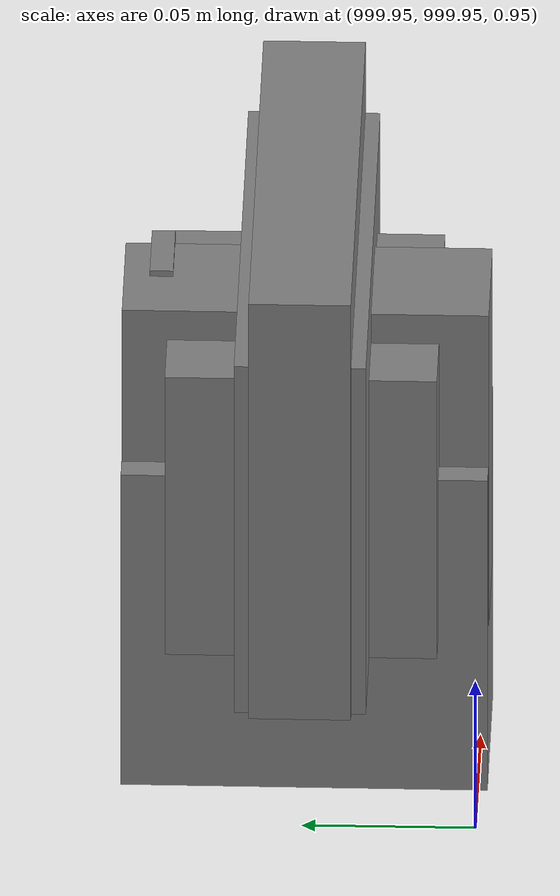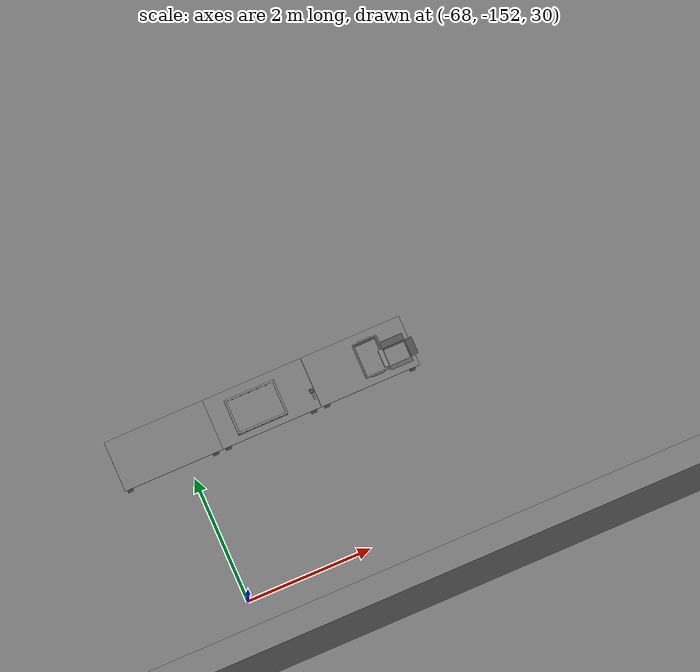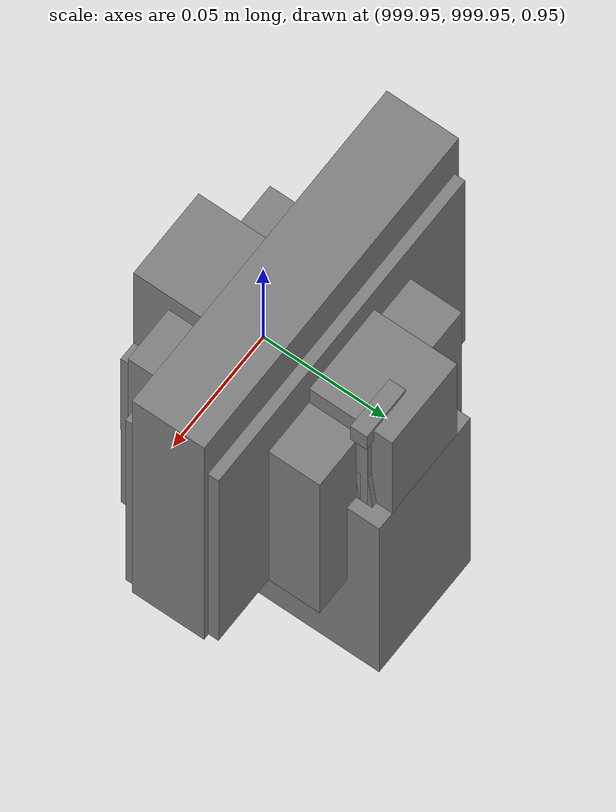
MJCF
<mujoco>
    <option gravity="0.000000000 0.000000000 -9.810000420" timestep="0.0049999999" integrator="implicitfast" density="1.225" viscosity="1.8000001e-05" noslip_iterations="10" iterations="100" sdf_iterations="50">
        <flag multiccd="disable"/>
    </option>
    <size memory="1000M"/>
    <compiler coordinate="local"/>
    <worldbody>
        <light cutoff="30" pos="0 1 1" dir="0 -1 -2"/>
        <light cutoff="30" pos="0 -1 1" dir="0 1 -2"/>
        <body pos="-64.866622925 -149.383972168 30.183746338" euler="89.999984741 89.999946594 0.000000000" name="openloong_gripper_2f85_fix_base_usda_bluebox_01">
            <geom contype="1" conaffinity="1" density="1000" type="box" material="" rgba="0.500000000 0.500000000 0.500000000 1.000000000" solimp="0.899999976 0.949999988 0.001000000" friction="1.000000000 0.005000000 0.000100000" solref="0.020000000 1.000000000" margin="0" condim="3" group="0" pos="0.276580811 0.187225342 0.000068665" quat="0.707106948 0.000077471 0.707106352 0.000077486" size="0.100000001 0.057999998 0.010000000" name="openloong_gripper_2f85_fix_base_usda_geom_E17887B9_33DA_4152_BCA2_58E23BF7F94F"/>
            <geom contype="1" conaffinity="1" density="1000" type="box" material="" rgba="0.500000000 0.500000000 0.500000000 1.000000000" solimp="0.899999976 0.949999988 0.001000000" friction="1.000000000 0.005000000 0.000100000" solref="0.020000000 1.000000000" margin="0" condim="3" group="0" pos="0.000000000 0.002883911 0.000000000" quat="0.999999881 0.000000000 0.000000000 0.000000000" size="0.254000008 0.003000000 0.172000006" name="openloong_gripper_2f85_fix_base_usda_geom_A93E05AD_8701_44F5_9BAD_C5EB8C88D78D"/>
            <geom contype="1" conaffinity="1" density="1000" type="box" material="" rgba="0.500000000 0.500000000 0.500000000 1.000000000" solimp="0.899999976 0.949999988 0.001000000" friction="1.000000000 0.005000000 0.000100000" solref="0.020000000 1.000000000" margin="0" condim="3" group="0" pos="0.000000000 0.124874115 0.173484802" quat="0.999796331 0.020176515 -0.000000015 0.000000030" size="0.259999990 0.119999997 0.007000000" name="openloong_gripper_2f85_fix_base_usda_geom_76CCAA47_526C_4B50_9B17_918171271EEE"/>
            <geom contype="1" conaffinity="1" density="1000" type="box" material="" rgba="0.500000000 0.500000000 0.500000000 1.000000000" solimp="0.899999976 0.949999988 0.001000000" friction="1.000000000 0.005000000 0.000100000" solref="0.020000000 1.000000000" margin="0" condim="3" group="0" pos="0.000000000 0.124874115 -0.173469543" quat="0.999796331 -0.020176545 -0.000000015 0.000000000" size="0.259999990 0.119999997 0.007000000" name="openloong_gripper_2f85_fix_base_usda_geom_C896D69B_3454_422C_9364_C0FE0BE90AFD"/>
            <geom contype="1" conaffinity="1" density="1000" type="box" material="" rgba="0.500000000 0.500000000 0.500000000 1.000000000" solimp="0.899999976 0.949999988 0.001000000" friction="1.000000000 0.005000000 0.000100000" solref="0.020000000 1.000000000" margin="0" condim="3" group="0" pos="0.000000000 0.214008331 0.188980103" quat="0.999912977 0.013176724 0.000000015 0.000000000" size="0.259999990 0.029999999 0.012500000" name="openloong_gripper_2f85_fix_base_usda_geom_6381C732_92BD_4280_821E_0C9DA7337CF1"/>
            <geom contype="1" conaffinity="1" density="1000" type="box" material="" rgba="0.500000000 0.500000000 0.500000000 1.000000000" solimp="0.899999976 0.949999988 0.001000000" friction="1.000000000 0.005000000 0.000100000" solref="0.020000000 1.000000000" margin="0" condim="3" group="0" pos="-0.258361816 0.125289917 0.001876831" quat="0.702796936 -0.020792112 0.710783124 0.020769298" size="0.189999998 0.119999997 0.009000000" name="openloong_gripper_2f85_fix_base_usda_geom_2F843B4E_5DC5_48CC_8591_1E870758A87D"/>
            <geom contype="1" conaffinity="1" density="1000" type="box" material="" rgba="0.500000000 0.500000000 0.500000000 1.000000000" solimp="0.899999976 0.949999988 0.001000000" friction="1.000000000 0.005000000 0.000100000" solref="0.020000000 1.000000000" margin="0" condim="3" group="0" pos="0.000000000 0.214008331 -0.188980103" quat="0.999912977 -0.013176769 0.000000030 0.000000015" size="0.259999990 0.029999999 0.012500000" name="openloong_gripper_2f85_fix_base_usda_geom_D2DF1040_02E9_4468_8849_EC7F36ABD3F5"/>
            <geom contype="1" conaffinity="1" density="1000" type="box" material="" rgba="0.500000000 0.500000000 0.500000000 1.000000000" solimp="0.899999976 0.949999988 0.001000000" friction="1.000000000 0.005000000 0.000100000" solref="0.020000000 1.000000000" margin="0" condim="3" group="0" pos="-0.276611328 0.187225342 0.000068665" quat="0.707106650 0.000077441 0.707106709 0.000077456" size="0.100000001 0.057999998 0.010000000" name="openloong_gripper_2f85_fix_base_usda_geom_DEB30D4C_3780_4360_B3F0_D530DAE59C8F"/>
            <geom contype="1" conaffinity="1" density="1000" type="box" material="" rgba="0.500000000 0.500000000 0.500000000 1.000000000" solimp="0.899999976 0.949999988 0.001000000" friction="1.000000000 0.005000000 0.000100000" solref="0.020000000 1.000000000" margin="0" condim="3" group="0" pos="0.258331299 0.125289917 0.001876831" quat="0.702851415 0.018856421 0.710823774 -0.019329369" size="0.189999998 0.119999997 0.009000000" name="openloong_gripper_2f85_fix_base_usda_geom_689E429B_0643_4F84_974F_098307A78A7A"/>
            <freejoint name="openloong_gripper_2f85_fix_base_usda_bluebox_01_joint"/>
            <site size="0.005000000 0.005000000 0.005000000" rgba="0.500000000 0.500000000 0.500000000 1.000000000" pos="0.000000000 0.000000000 0.000000000" quat="0.999961913 0.008726534 0.000000000 0.000000000" group="0" type="sphere" name="openloong_gripper_2f85_fix_base_usda_bluebox_01site"/>
        </body>
        <body pos="-64.496299744 -149.491867065 30.235729218" euler="0.000000000 0.000000000 89.999946594" name="openloong_gripper_2f85_fix_base_usda_cardboardbox_01">
            <geom contype="1" conaffinity="1" density="1000" type="box" material="" rgba="0.500000000 0.500000000 0.500000000 1.000000000" solimp="0.899999976 0.949999988 0.001000000" friction="1.000000000 0.005000000 0.000100000" solref="0.020000000 1.000000000" margin="0" condim="3" group="0" pos="-0.003166199 -0.004086494 0.005052090" quat="1.000000000 0.000000000 0.000000000 0.000000000" size="0.142499998 0.177500010 0.005000000" name="openloong_gripper_2f85_fix_base_usda_geom_59BBFD44_C6B9_4BD2_A94D_6488FEB28F5B"/>
            <geom contype="1" conaffinity="1" density="1000" type="box" material="" rgba="0.500000000 0.500000000 0.500000000 1.000000000" solimp="0.899999976 0.949999988 0.001000000" friction="1.000000000 0.005000000 0.000100000" solref="0.020000000 1.000000000" margin="0" condim="3" group="0" pos="-0.003166199 0.170316696 0.150570869" quat="1.000000000 0.000000000 0.000000000 0.000000000" size="0.142499998 0.005000000 0.149999991" name="openloong_gripper_2f85_fix_base_usda_geom_01F711EA_BDA6_4B84_A33E_F9F39BF1E917"/>
            <geom contype="1" conaffinity="1" density="1000" type="box" material="" rgba="0.500000000 0.500000000 0.500000000 1.000000000" solimp="0.899999976 0.949999988 0.001000000" friction="1.000000000 0.005000000 0.000100000" solref="0.020000000 1.000000000" margin="0" condim="3" group="0" pos="-0.147399902 -0.005307198 0.150570869" quat="1.000000000 0.000000000 0.000000000 0.000000000" size="0.005000000 0.177500010 0.149999991" name="openloong_gripper_2f85_fix_base_usda_geom_308BF358_97D6_43AE_B275_FC9997843AB8"/>
            <geom contype="1" conaffinity="1" density="1000" type="box" material="" rgba="0.500000000 0.500000000 0.500000000 1.000000000" solimp="0.899999976 0.949999988 0.001000000" friction="1.000000000 0.005000000 0.000100000" solref="0.020000000 1.000000000" margin="0" condim="3" group="0" pos="0.140275955 -0.005307198 0.150570869" quat="1.000000000 0.000000000 0.000000000 0.000000000" size="0.005000000 0.177500010 0.149999991" name="openloong_gripper_2f85_fix_base_usda_geom_998ACB1D_B1F3_4375_B4A1_91451AAE432E"/>
            <geom contype="1" conaffinity="1" density="1000" type="box" material="" rgba="0.500000000 0.500000000 0.500000000 1.000000000" solimp="0.899999976 0.949999988 0.001000000" friction="1.000000000 0.005000000 0.000100000" solref="0.020000000 1.000000000" margin="0" condim="3" group="0" pos="-0.003166199 -0.181550980 0.150570869" quat="1.000000000 0.000000000 0.000000000 0.000000000" size="0.142499998 0.005000000 0.149999991" name="openloong_gripper_2f85_fix_base_usda_geom_D40528E8_5FB4_480D_945A_7F18F1610710"/>
            <freejoint name="openloong_gripper_2f85_fix_base_usda_cardboardbox_01_joint"/>
            <site size="0.005000000 0.005000000 0.005000000" rgba="0.500000000 0.500000000 0.500000000 1.000000000" pos="0.000000000 0.000000000 0.000000000" quat="0.999961913 0.008726535 0.000000000 0.000000000" group="0" type="sphere" name="openloong_gripper_2f85_fix_base_usda_site_1C2BF00C_5006_4178_BDC9_6578C88F565A"/>
            <body pos="0.139160156 -0.004048347 0.301930904" euler="-179.999954224 49.383502960 179.999954224" name="openloong_gripper_2f85_fix_base_usda_A1_006">
                <geom contype="1" conaffinity="1" density="1000" type="box" material="" rgba="0.500000000 0.500000000 0.500000000 1.000000000" solimp="0.899999976 0.949999988 0.001000000" friction="1.000000000 0.005000000 0.000100000" solref="0.020000000 1.000000000" margin="0" condim="3" group="0" pos="-0.071587563 0.000009537 0.001745224" quat="0.999999881 0.000000000 0.000000000 0.000000000" size="0.071249999 0.179999992 0.002500000" name="openloong_gripper_2f85_fix_base_usda_geom_21D009D2_10A0_4A3C_8DD7_4ADF66E983BA"/>
                <joint armature="0" stiffness="0.07" damping="0.0099999998" axis="0.000000 1.000000 0.000000" type="hinge" name="openloong_gripper_2f85_fix_base_usda_A1_006"/>
            </body>
            <body pos="-0.145902634 -0.004086494 0.301938057" euler="-180.000000000 -60.000011444 -180.000000000" name="openloong_gripper_2f85_fix_base_usda_A2_006">
                <geom contype="1" conaffinity="1" density="1000" type="box" material="" rgba="0.500000000 0.500000000 0.500000000 1.000000000" solimp="0.899999976 0.949999988 0.001000000" friction="1.000000000 0.005000000 0.000100000" solref="0.020000000 1.000000000" margin="0" condim="3" group="0" pos="0.071268082 0.000009537 0.002717972" quat="0.000002921 0.000000000 -0.000000030 0.999999881" size="0.071249999 0.179999992 0.002500000" name="openloong_gripper_2f85_fix_base_usda_geom_991A21E1_CAC7_45D9_8BB3_9788BAC5E355"/>
                <joint armature="0" stiffness="0.07" damping="0.0099999998" axis="0.000000 1.000000 0.000000" type="hinge" name="openloong_gripper_2f85_fix_base_usda_A2_006"/>
            </body>
            <body pos="-0.003385544 0.175991058 0.301930904" euler="-125.858116150 -0.000004561 0.000002331" name="openloong_gripper_2f85_fix_base_usda_B2_006">
                <geom contype="1" conaffinity="1" density="1000" type="box" material="" rgba="0.500000000 0.500000000 0.500000000 1.000000000" solimp="0.899999976 0.949999988 0.001000000" friction="1.000000000 0.005000000 0.000100000" solref="0.020000000 1.000000000" margin="0" condim="3" group="0" pos="0.000009537 -0.070939064 -0.002470016" quat="0.999614120 0.027776197 -0.000000015 0.000000030" size="0.137500003 0.064999998 0.005000000" name="openloong_gripper_2f85_fix_base_usda_geom_61EC8FF4_C45F_4C3E_B93C_68413139D421"/>
                <joint armature="0" stiffness="0.07" damping="0.0099999998" axis="1.000000 0.000000 0.000000" type="hinge" name="openloong_gripper_2f85_fix_base_usda_B2_006"/>
            </body>
            <body pos="-0.003385544 -0.184140205 0.301938057" euler="147.805557251 0.000000000 0.000000000" name="openloong_gripper_2f85_fix_base_usda_B1_006">
                <geom contype="1" conaffinity="1" density="1000" type="box" material="" rgba="0.500000000 0.500000000 0.500000000 1.000000000" solimp="0.899999976 0.949999988 0.001000000" friction="1.000000000 0.005000000 0.000100000" solref="0.020000000 1.000000000" margin="0" condim="3" group="0" pos="-0.000028610 0.070202351 -0.002703667" quat="0.999614179 -0.027776167 0.000000000 0.000000000" size="0.137500003 0.064999998 0.005000000" name="openloong_gripper_2f85_fix_base_usda_geom_1C497B2E_19B4_4BDE_B271_E6316A791756"/>
                <joint armature="0" stiffness="0.07" damping="0.0099999998" axis="1.000000 0.000000 0.000000" type="hinge" name="openloong_gripper_2f85_fix_base_usda_B1_006"/>
            </body>
        </body>
        <body pos="-65.882858276 -149.481979370 30.229999542" euler="-64.487716675 0.000000000 0.000000000" name="openloong_gripper_2f85_fix_base_usda_Barcode">
            <geom contype="1" conaffinity="1" density="1000" type="box" material="" rgba="0.500000000 0.500000000 0.500000000 1.000000000" solimp="0.899999976 0.949999988 0.001000000" friction="1.000000000 0.005000000 0.000100000" solref="0.020000000 1.000000000" margin="0" condim="3" group="0" pos="0.000000000 0.013038635 0.001419067" quat="0.000000000 0.000000000 0.000000000 1.000000119" size="0.034000002 0.010000000 0.017999999" name="openloong_gripper_2f85_fix_base_usda_geom_4BD01BB0_BD39_4E9B_9FAD_9AD9CFEA9BC0"/>
            <geom contype="1" conaffinity="1" density="1000" type="box" material="" rgba="0.500000000 0.500000000 0.500000000 1.000000000" solimp="0.899999976 0.949999988 0.001000000" friction="1.000000000 0.005000000 0.000100000" solref="0.020000000 1.000000000" margin="0" condim="3" group="0" pos="0.000000000 -0.035301208 -0.007095337" quat="0.000000000 0.000000000 -0.043619365 0.999048233" size="0.028999999 0.010000000 0.020000000" name="openloong_gripper_2f85_fix_base_usda_geom_D3276004_78A6_4DAE_BDE0_ACFFEDB503D8"/>
            <geom contype="1" conaffinity="1" density="1000" type="box" material="" rgba="0.500000000 0.500000000 0.500000000 1.000000000" solimp="0.899999976 0.949999988 0.001000000" friction="1.000000000 0.005000000 0.000100000" solref="0.020000000 1.000000000" margin="0" condim="3" group="0" pos="0.000000000 -0.043411255 -0.011749268" quat="0.922262907 0.386563420 0.000000000 0.000000000" size="0.026000001 0.010000000 0.020000000" name="openloong_gripper_2f85_fix_base_usda_geom_46C0149C_9C7C_4931_8144_D5027BCF3F13"/>
            <geom contype="1" conaffinity="1" density="1000" type="box" material="" rgba="0.500000000 0.500000000 0.500000000 1.000000000" solimp="0.899999976 0.949999988 0.001000000" friction="1.000000000 0.005000000 0.000100000" solref="0.020000000 1.000000000" margin="0" condim="3" group="0" pos="0.000000000 -0.016967773 -0.031860352" quat="0.000000000 0.000000000 0.000000000 1.000000119" size="0.008000000 0.010000000 0.013000000" name="openloong_gripper_2f85_fix_base_usda_geom_DA875AB0_E810_4FE5_B883_67FD1F8135CB"/>
            <geom contype="1" conaffinity="1" density="1000" type="box" material="" rgba="0.500000000 0.500000000 0.500000000 1.000000000" solimp="0.899999976 0.949999988 0.001000000" friction="1.000000000 0.005000000 0.000100000" solref="0.020000000 1.000000000" margin="0" condim="3" group="0" pos="0.000000000 -0.001869202 0.000312805" quat="0.953716993 0.300705761 0.000000000 0.000000000" size="0.032000002 0.010000000 0.018999999" name="openloong_gripper_2f85_fix_base_usda_geom_49D574D5_9A66_400F_98E5_1A174532462B"/>
            <geom contype="1" conaffinity="1" density="1000" type="box" material="" rgba="0.500000000 0.500000000 0.500000000 1.000000000" solimp="0.899999976 0.949999988 0.001000000" friction="1.000000000 0.005000000 0.000100000" solref="0.020000000 1.000000000" margin="0" condim="3" group="0" pos="0.000000000 -0.019531250 -0.003173828" quat="0.953716993 0.300705761 0.000000000 0.000000000" size="0.030999999 0.010000000 0.020000000" name="openloong_gripper_2f85_fix_base_usda_geom_365F3AAB_6146_42A2_9025_125F351B3578"/>
            <geom contype="1" conaffinity="1" density="1000" type="box" material="" rgba="0.500000000 0.500000000 0.500000000 1.000000000" solimp="0.899999976 0.949999988 0.001000000" friction="1.000000000 0.005000000 0.000100000" solref="0.020000000 1.000000000" margin="0" condim="3" group="0" pos="0.000000000 -0.035301208 -0.007095337" quat="0.953716993 0.300705761 0.000000000 0.000000000" size="0.028999999 0.010000000 0.020000000" name="openloong_gripper_2f85_fix_base_usda_geom_9D85293B_82CE_4428_9E11_1ACA8A2485F0"/>
            <geom contype="1" conaffinity="1" density="1000" type="box" material="" rgba="0.500000000 0.500000000 0.500000000 1.000000000" solimp="0.899999976 0.949999988 0.001000000" friction="1.000000000 0.005000000 0.000100000" solref="0.020000000 1.000000000" margin="0" condim="3" group="0" pos="0.000000000 -0.042617798 -0.071121216" quat="0.000000000 0.000000000 0.000000000 1.000000119" size="0.013000000 0.021000000 0.059999999" name="openloong_gripper_2f85_fix_base_usda_geom_3DCBF0E2_12DF_419D_82DD_7849A3BA4AF0"/>
            <freejoint name="openloong_gripper_2f85_fix_base_usda_Barcode_joint"/>
            <site size="0.005000000 0.005000000 0.005000000" rgba="0.500000000 0.500000000 0.500000000 1.000000000" pos="0.000000000 0.000000000 0.000000000" quat="1.000000000 0.000000000 0.000000000 0.000000000" group="0" type="sphere" name="openloong_gripper_2f85_fix_base_usda_Barcode_site"/>
        </body>
        <body pos="-66.745018005 -149.392349243 30.184000015" euler="0.000000000 0.000000000 89.999946594" name="[22330220738331]_Basket_01">
            <geom contype="1" conaffinity="1" density="1000" type="box" material="" rgba="0.500000000 0.500000000 0.500000000 1.000000000" solimp="0.899999976 0.949999988 0.001000000" friction="1.000000000 0.005000000 0.000100000" solref="0.020000000 1.000000000" margin="0" condim="3" group="0" pos="-0.052425385 0.389207840 0.089787483" quat="0.707107008 0.000000000 0.000000000 0.707106411" size="0.014249999 0.014249999 0.059999999" name="[22330220738331]_geom_29B66EAE_D6BB_4206_9276_5CDB55D00956"/>
            <geom contype="1" conaffinity="1" density="1000" type="box" material="" rgba="0.500000000 0.500000000 0.500000000 1.000000000" solimp="0.899999976 0.949999988 0.001000000" friction="1.000000000 0.005000000 0.000100000" solref="0.020000000 1.000000000" margin="0" condim="3" group="0" pos="0.264015198 -0.133043289 0.089787483" quat="0.707107008 0.000000000 0.000000000 0.707106411" size="0.014249999 0.014249999 0.059999999" name="[22330220738331]_geom_CBF50C20_418A_4964_BA0A_CB27BE6107EF"/>
            <geom contype="1" conaffinity="1" density="1000" type="box" material="" rgba="0.500000000 0.500000000 0.500000000 1.000000000" solimp="0.899999976 0.949999988 0.001000000" friction="1.000000000 0.005000000 0.000100000" solref="0.020000000 1.000000000" margin="0" condim="3" group="0" pos="-0.264015198 -0.265548706 0.089793205" quat="0.707107008 0.000000000 0.000000000 0.707106411" size="0.014249999 0.014249999 0.059999999" name="[22330220738331]_geom_8CBABBF4_FC9D_431B_86BA_EEE504B2B80C"/>
            <geom contype="1" conaffinity="1" density="1000" type="box" material="" rgba="0.500000000 0.500000000 0.500000000 1.000000000" solimp="0.899999976 0.949999988 0.001000000" friction="1.000000000 0.005000000 0.000100000" solref="0.020000000 1.000000000" margin="0" condim="3" group="0" pos="-0.160263062 -0.389322281 0.089793205" quat="0.707107008 0.000000000 0.000000000 0.707106411" size="0.014249999 0.014249999 0.059999999" name="[22330220738331]_geom_479F0FFB_2384_42F9_9904_791D89DF6236"/>
            <geom contype="1" conaffinity="1" density="1000" type="box" material="" rgba="0.500000000 0.500000000 0.500000000 1.000000000" solimp="0.899999976 0.949999988 0.001000000" friction="1.000000000 0.005000000 0.000100000" solref="0.020000000 1.000000000" margin="0" condim="3" group="0" pos="0.162265778 -0.389322281 0.089787483" quat="0.707107008 0.000000000 0.000000000 0.707106411" size="0.014249999 0.014249999 0.059999999" name="[22330220738331]_geom_F3D3D1B6_A154_40BD_AD45_9B6000E3ADD7"/>
            <geom contype="1" conaffinity="1" density="1000" type="box" material="" rgba="0.500000000 0.500000000 0.500000000 1.000000000" solimp="0.899999976 0.949999988 0.001000000" friction="1.000000000 0.005000000 0.000100000" solref="0.020000000 1.000000000" margin="0" condim="3" group="0" pos="0.264015198 0.389207840 0.089787483" quat="0.707107008 0.000000000 0.000000000 0.707106411" size="0.014249999 0.014249999 0.059999999" name="[22330220738331]_geom_4416CCA5_7106_4426_9A61_3337644AC026"/>
            <geom contype="1" conaffinity="1" density="1000" type="box" material="" rgba="0.500000000 0.500000000 0.500000000 1.000000000" solimp="0.899999976 0.949999988 0.001000000" friction="1.000000000 0.005000000 0.000100000" solref="0.020000000 1.000000000" margin="0" condim="3" group="0" pos="-0.264015198 -0.133043289 0.089793205" quat="0.707107008 0.000000000 0.000000000 0.707106411" size="0.014249999 0.014249999 0.059999999" name="[22330220738331]_geom_BFDAF0FC_04E0_472F_9C98_0D0631ADC569"/>
            <geom contype="1" conaffinity="1" density="1000" type="box" material="" rgba="0.500000000 0.500000000 0.500000000 1.000000000" solimp="0.899999976 0.949999988 0.001000000" friction="1.000000000 0.005000000 0.000100000" solref="0.020000000 1.000000000" margin="0" condim="3" group="0" pos="-0.264026642 0.269256592 0.089793205" quat="0.707107008 0.000000000 0.000000000 0.707106411" size="0.014249999 0.014249999 0.059999999" name="[22330220738331]_geom_C151CF38_6209_4D2A_9CF0_129B35B5D121"/>
            <geom contype="1" conaffinity="1" density="1000" type="box" material="" rgba="0.500000000 0.500000000 0.500000000 1.000000000" solimp="0.899999976 0.949999988 0.001000000" friction="1.000000000 0.005000000 0.000100000" solref="0.020000000 1.000000000" margin="0" condim="3" group="0" pos="0.054462433 0.389207840 0.089787483" quat="0.707107008 0.000000000 0.000000000 0.707106411" size="0.014249999 0.014249999 0.059999999" name="[22330220738331]_geom_F4FCEBFE_987B_48D7_88CC_25E8EC8DD175"/>
            <geom contype="1" conaffinity="1" density="1000" type="box" material="" rgba="0.500000000 0.500000000 0.500000000 1.000000000" solimp="0.899999976 0.949999988 0.001000000" friction="1.000000000 0.005000000 0.000100000" solref="0.020000000 1.000000000" margin="0" condim="3" group="0" pos="0.054462433 -0.389322281 0.089787483" quat="0.707107008 0.000000000 0.000000000 0.707106411" size="0.014249999 0.014249999 0.059999999" name="[22330220738331]_geom_640A542E_1121_4BD5_A2BA_6637D52E4AA7"/>
            <geom contype="1" conaffinity="1" density="1000" type="box" material="" rgba="0.500000000 0.500000000 0.500000000 1.000000000" solimp="0.899999976 0.949999988 0.001000000" friction="1.000000000 0.005000000 0.000100000" solref="0.020000000 1.000000000" margin="0" condim="3" group="0" pos="0.264015198 0.269256592 0.089793205" quat="0.707107008 0.000000000 0.000000000 0.707106411" size="0.014249999 0.014249999 0.059999999" name="[22330220738331]_geom_E878E5C3_C868_4393_87D8_618FC790BBF6"/>
            <geom contype="1" conaffinity="1" density="1000" type="box" material="" rgba="0.500000000 0.500000000 0.500000000 1.000000000" solimp="0.899999976 0.949999988 0.001000000" friction="1.000000000 0.005000000 0.000100000" solref="0.020000000 1.000000000" margin="0" condim="3" group="0" pos="0.264015198 -0.389322281 0.089787483" quat="0.707107008 0.000000000 0.000000000 0.707106411" size="0.014249999 0.014249999 0.059999999" name="[22330220738331]_geom_1CE27328_93F1_4E56_9E7C_5CE5AAB5C206"/>
            <geom contype="1" conaffinity="1" density="1000" type="box" material="" rgba="0.500000000 0.500000000 0.500000000 1.000000000" solimp="0.899999976 0.949999988 0.001000000" friction="1.000000000 0.005000000 0.000100000" solref="0.020000000 1.000000000" margin="0" condim="3" group="0" pos="0.000000000 0.000000000 0.015998840" quat="0.707107008 0.000000000 0.000000000 0.707106411" size="0.403499991 0.279000014 0.015750000" name="[22330220738331]_geom_DF4CA6BA_7442_4D4B_BD03_104DFE45B414"/>
            <geom contype="1" conaffinity="1" density="1000" type="box" material="" rgba="0.500000000 0.500000000 0.500000000 1.000000000" solimp="0.899999976 0.949999988 0.001000000" friction="1.000000000 0.005000000 0.000100000" solref="0.020000000 1.000000000" margin="0" condim="3" group="0" pos="0.000000000 -0.389476776 0.163619041" quat="0.707107008 0.000000000 0.000000000 0.707106411" size="0.015000000 0.277500004 0.015750000" name="[22330220738331]_geom_F1150273_78EA_4748_8E37_9C9109BB6B67"/>
            <geom contype="1" conaffinity="1" density="1000" type="box" material="" rgba="0.500000000 0.500000000 0.500000000 1.000000000" solimp="0.899999976 0.949999988 0.001000000" friction="1.000000000 0.005000000 0.000100000" solref="0.020000000 1.000000000" margin="0" condim="3" group="0" pos="0.162265778 0.389207840 0.089787483" quat="0.707107008 0.000000000 0.000000000 0.707106411" size="0.014249999 0.014249999 0.059999999" name="[22330220738331]_geom_57261914_141D_46D6_A9D2_8BB1BBC2E0B0"/>
            <geom contype="1" conaffinity="1" density="1000" type="box" material="" rgba="0.500000000 0.500000000 0.500000000 1.000000000" solimp="0.899999976 0.949999988 0.001000000" friction="1.000000000 0.005000000 0.000100000" solref="0.020000000 1.000000000" margin="0" condim="3" group="0" pos="0.000000000 0.389471054 0.163619041" quat="0.707107008 0.000000000 0.000000000 0.707106411" size="0.015000000 0.277500004 0.015750000" name="[22330220738331]_geom_42B9CC23_B1F1_41C2_861F_37A636ABDE35"/>
            <geom contype="1" conaffinity="1" density="1000" type="box" material="" rgba="0.500000000 0.500000000 0.500000000 1.000000000" solimp="0.899999976 0.949999988 0.001000000" friction="1.000000000 0.005000000 0.000100000" solref="0.020000000 1.000000000" margin="0" condim="3" group="0" pos="-0.263511658 0.000000000 0.163619041" quat="0.707107008 0.000000000 0.000000000 0.707106411" size="0.403499991 0.015000000 0.015750000" name="[22330220738331]_geom_15855701_AF68_41CA_999A_EEEC1FB5A422"/>
            <geom contype="1" conaffinity="1" density="1000" type="box" material="" rgba="0.500000000 0.500000000 0.500000000 1.000000000" solimp="0.899999976 0.949999988 0.001000000" friction="1.000000000 0.005000000 0.000100000" solref="0.020000000 1.000000000" margin="0" condim="3" group="0" pos="-0.264015198 0.141334534 0.089793205" quat="0.707107008 0.000000000 0.000000000 0.707106411" size="0.014249999 0.014249999 0.059999999" name="[22330220738331]_geom_05FD3E15_9230_4777_A058_DE62CB8993E1"/>
            <geom contype="1" conaffinity="1" density="1000" type="box" material="" rgba="0.500000000 0.500000000 0.500000000 1.000000000" solimp="0.899999976 0.949999988 0.001000000" friction="1.000000000 0.005000000 0.000100000" solref="0.020000000 1.000000000" margin="0" condim="3" group="0" pos="0.264015198 -0.265548706 0.089787483" quat="0.707107008 0.000000000 0.000000000 0.707106411" size="0.014249999 0.014249999 0.059999999" name="[22330220738331]_geom_12B3C63F_AD26_4DCA_A5D5_C6BBC81EAA2C"/>
            <geom contype="1" conaffinity="1" density="1000" type="box" material="" rgba="0.500000000 0.500000000 0.500000000 1.000000000" solimp="0.899999976 0.949999988 0.001000000" friction="1.000000000 0.005000000 0.000100000" solref="0.020000000 1.000000000" margin="0" condim="3" group="0" pos="-0.160263062 0.389207840 0.089787483" quat="0.707107008 0.000000000 0.000000000 0.707106411" size="0.014249999 0.014249999 0.059999999" name="[22330220738331]_geom_098ADA0F_592B_4D9B_9B4D_E93F440F6EEB"/>
            <geom contype="1" conaffinity="1" density="1000" type="box" material="" rgba="0.500000000 0.500000000 0.500000000 1.000000000" solimp="0.899999976 0.949999988 0.001000000" friction="1.000000000 0.005000000 0.000100000" solref="0.020000000 1.000000000" margin="0" condim="3" group="0" pos="-0.052425385 -0.389322281 0.089787483" quat="0.707107008 0.000000000 0.000000000 0.707106411" size="0.014249999 0.014249999 0.059999999" name="[22330220738331]_geom_969322F0_4377_48E6_B335_60EE364EB786"/>
            <geom contype="1" conaffinity="1" density="1000" type="box" material="" rgba="0.500000000 0.500000000 0.500000000 1.000000000" solimp="0.899999976 0.949999988 0.001000000" friction="1.000000000 0.005000000 0.000100000" solref="0.020000000 1.000000000" margin="0" condim="3" group="0" pos="-0.264026642 -0.389322281 0.089793205" quat="0.707107008 0.000000000 0.000000000 0.707106411" size="0.014249999 0.014249999 0.059999999" name="[22330220738331]_geom_23C7C66D_0896_41CF_B40D_A84319E30048"/>
            <geom contype="1" conaffinity="1" density="1000" type="box" material="" rgba="0.500000000 0.500000000 0.500000000 1.000000000" solimp="0.899999976 0.949999988 0.001000000" friction="1.000000000 0.005000000 0.000100000" solref="0.020000000 1.000000000" margin="0" condim="3" group="0" pos="0.264015198 0.141334534 0.089787483" quat="0.707107008 0.000000000 0.000000000 0.707106411" size="0.014249999 0.014249999 0.059999999" name="[22330220738331]_geom_69CF12EF_77B6_45FC_A0E4_E33C494EF398"/>
            <geom contype="1" conaffinity="1" density="1000" type="box" material="" rgba="0.500000000 0.500000000 0.500000000 1.000000000" solimp="0.899999976 0.949999988 0.001000000" friction="1.000000000 0.005000000 0.000100000" solref="0.020000000 1.000000000" margin="0" condim="3" group="0" pos="-0.264015198 0.389207840 0.089793205" quat="0.707107008 0.000000000 0.000000000 0.707106411" size="0.014249999 0.014249999 0.059999999" name="[22330220738331]_geom_1DABB26F_F4F5_4E21_AF70_1413E7F147E2"/>
            <geom contype="1" conaffinity="1" density="1000" type="box" material="" rgba="0.500000000 0.500000000 0.500000000 1.000000000" solimp="0.899999976 0.949999988 0.001000000" friction="1.000000000 0.005000000 0.000100000" solref="0.020000000 1.000000000" margin="0" condim="3" group="0" pos="0.264015198 0.004480362 0.089787483" quat="0.707107008 0.000000000 0.000000000 0.707106411" size="0.014249999 0.014249999 0.059999999" name="[22330220738331]_geom_F7D9D447_7276_4BE5_98C1_745F6BDBBA63"/>
            <geom contype="1" conaffinity="1" density="1000" type="box" material="" rgba="0.500000000 0.500000000 0.500000000 1.000000000" solimp="0.899999976 0.949999988 0.001000000" friction="1.000000000 0.005000000 0.000100000" solref="0.020000000 1.000000000" margin="0" condim="3" group="0" pos="0.263694763 -0.000011444 0.163619041" quat="0.707107008 0.000000000 0.000000000 0.707106411" size="0.403499991 0.015000000 0.015750000" name="[22330220738331]_geom_3A7335B2_4624_4D91_84BE_D9CCE7B45BC1"/>
            <geom contype="1" conaffinity="1" density="1000" type="box" material="" rgba="0.500000000 0.500000000 0.500000000 1.000000000" solimp="0.899999976 0.949999988 0.001000000" friction="1.000000000 0.005000000 0.000100000" solref="0.020000000 1.000000000" margin="0" condim="3" group="0" pos="-0.264015198 0.004480362 0.089793205" quat="0.707107008 0.000000000 0.000000000 0.707106411" size="0.014249999 0.014249999 0.059999999" name="[22330220738331]_geom_871364BF_3630_43BF_873B_19D274E86298"/>
            <freejoint name="[22330220738331]_joint_B806E39C_31D7_42A0_9875_26FDBA8C8FF1"/>
        </body>
        <body pos="0.000000000 0.000000000 0.000000000" euler="0.000000000 0.000000000 0.000000000" name="Static Objects_Static Objects">
            <geom contype="1" conaffinity="1" density="1000" type="box" material="" rgba="0.500000000 0.500000000 0.500000000 1.000000000" solimp="0.899999976 0.949999988 0.001000000" friction="1.000000000 0.005000000 0.000100000" solref="0.020000000 1.000000000" margin="0" condim="3" group="0" pos="-67.544113159 -149.365814209 29.727830887" quat="0.500000417 0.499999970 0.499999553 0.499999970" size="0.381000012 0.319999993 0.041000001" name="Static Objects_geom_3A181889_DEA7_4AEF_BC4F_356BC3D293E7"/>
            <geom contype="1" conaffinity="1" density="1000" type="box" material="" rgba="0.500000000 0.500000000 0.500000000 1.000000000" solimp="0.899999976 0.949999988 0.001000000" friction="1.000000000 0.005000000 0.000100000" solref="0.020000000 1.000000000" margin="0" condim="3" group="0" pos="-68.239501953 -149.365814209 30.086868286" quat="0.500000417 0.499999970 0.499999553 0.499999970" size="0.370999992 0.039500002 0.745000005" name="Static Objects_geom_D39976F3_9868_4E17_AA3D_0D12201B8F79"/>
            <geom contype="1" conaffinity="1" density="1000" type="box" material="" rgba="0.500000000 0.500000000 0.500000000 1.000000000" solimp="0.899999976 0.949999988 0.001000000" friction="1.000000000 0.005000000 0.000100000" solref="0.020000000 1.000000000" margin="0" condim="3" group="0" pos="-68.239501953 -149.365814209 30.147235870" quat="0.500000417 0.499999970 0.499999553 0.499999970" size="0.400000006 0.022000000 0.800000012" name="Static Objects_geom_AA3340E8_B8BE_462F_866F_ED208E1CA239"/>
            <geom contype="1" conaffinity="1" density="1000" type="box" material="" rgba="0.500000000 0.500000000 0.500000000 1.000000000" solimp="0.899999976 0.949999988 0.001000000" friction="1.000000000 0.005000000 0.000100000" solref="0.020000000 1.000000000" margin="0" condim="3" group="0" pos="-68.934890747 -149.365814209 29.727830887" quat="0.500000417 0.499999970 0.499999553 0.499999970" size="0.381000012 0.319999993 0.041000001" name="Static Objects_geom_0C60153C_2D78_4E9B_9DC6_2D561EF098F2"/>
            <geom contype="1" conaffinity="1" density="1000" type="box" material="" rgba="0.500000000 0.500000000 0.500000000 1.000000000" solimp="0.899999976 0.949999988 0.001000000" friction="1.000000000 0.005000000 0.000100000" solref="0.020000000 1.000000000" margin="0" condim="3" group="0" pos="-68.239501953 -149.365814209 29.561563492" quat="0.500000417 0.499999970 0.499999553 0.499999970" size="0.020000000 0.022000000 0.660000026" name="Static Objects_geom_F08EE422_35C3_4E20_8CC9_87391EEF6D2F"/>
            <geom contype="1" conaffinity="1" density="1000" type="box" material="" rgba="0.500000000 0.500000000 0.500000000 1.000000000" solimp="0.899999976 0.949999988 0.001000000" friction="1.000000000 0.005000000 0.000100000" solref="0.020000000 1.000000000" margin="0" condim="3" group="0" pos="-65.945671082 -149.365814209 29.727830887" quat="0.500000417 0.499999970 0.499999553 0.499999970" size="0.381000012 0.319999993 0.041000001" name="Static Objects_geom_CA4391AA_C614_4027_A5C5_3915697F3176"/>
            <geom contype="1" conaffinity="1" density="1000" type="box" material="" rgba="0.500000000 0.500000000 0.500000000 1.000000000" solimp="0.899999976 0.949999988 0.001000000" friction="1.000000000 0.005000000 0.000100000" solref="0.020000000 1.000000000" margin="0" condim="3" group="0" pos="-66.641059875 -149.365814209 30.086868286" quat="0.500000417 0.499999970 0.499999553 0.499999970" size="0.370999992 0.039500002 0.745000005" name="Static Objects_geom_4D220A39_1DA5_47AB_ABB1_6BE96227DC2B"/>
            <geom contype="1" conaffinity="1" density="1000" type="box" material="" rgba="0.500000000 0.500000000 0.500000000 1.000000000" solimp="0.899999976 0.949999988 0.001000000" friction="1.000000000 0.005000000 0.000100000" solref="0.020000000 1.000000000" margin="0" condim="3" group="0" pos="-66.641059875 -149.365814209 30.147235870" quat="0.500000417 0.499999970 0.499999553 0.499999970" size="0.400000006 0.022000000 0.800000012" name="Static Objects_geom_5E82F81C_135F_4E89_9A77_7029C331C894"/>
            <geom contype="1" conaffinity="1" density="1000" type="box" material="" rgba="0.500000000 0.500000000 0.500000000 1.000000000" solimp="0.899999976 0.949999988 0.001000000" friction="1.000000000 0.005000000 0.000100000" solref="0.020000000 1.000000000" margin="0" condim="3" group="0" pos="-67.336448669 -149.365814209 29.727830887" quat="0.500000417 0.499999970 0.499999553 0.499999970" size="0.381000012 0.319999993 0.041000001" name="Static Objects_geom_91ABB247_5B3C_49F6_95FA_576CD5CDE6D4"/>
            <geom contype="1" conaffinity="1" density="1000" type="box" material="" rgba="0.500000000 0.500000000 0.500000000 1.000000000" solimp="0.899999976 0.949999988 0.001000000" friction="1.000000000 0.005000000 0.000100000" solref="0.020000000 1.000000000" margin="0" condim="3" group="0" pos="-66.641059875 -149.365814209 29.561563492" quat="0.500000417 0.499999970 0.499999553 0.499999970" size="0.020000000 0.022000000 0.660000026" name="Static Objects_geom_6750CD6C_BF03_4D8B_B46A_AD7A4B83E48C"/>
            <geom contype="1" conaffinity="1" density="1000" type="box" material="" rgba="0.500000000 0.500000000 0.500000000 1.000000000" solimp="0.899999976 0.949999988 0.001000000" friction="1.000000000 0.005000000 0.000100000" solref="0.020000000 1.000000000" margin="0" condim="3" group="0" pos="-64.338577271 -149.365814209 29.727830887" quat="0.500000417 0.499999970 0.499999553 0.499999970" size="0.381000012 0.319999993 0.041000001" name="Static Objects_geom_F091C4A2_90A4_47AC_901B_6F7BA6C2F33A"/>
            <geom contype="1" conaffinity="1" density="1000" type="box" material="" rgba="0.500000000 0.500000000 0.500000000 1.000000000" solimp="0.899999976 0.949999988 0.001000000" friction="1.000000000 0.005000000 0.000100000" solref="0.020000000 1.000000000" margin="0" condim="3" group="0" pos="-65.033966064 -149.365814209 30.086868286" quat="0.500000417 0.499999970 0.499999553 0.499999970" size="0.370999992 0.039500002 0.745000005" name="Static Objects_geom_8B8E1D6D_3A8F_43C0_8DC0_29B05D896E42"/>
            <geom contype="1" conaffinity="1" density="1000" type="box" material="" rgba="0.500000000 0.500000000 0.500000000 1.000000000" solimp="0.899999976 0.949999988 0.001000000" friction="1.000000000 0.005000000 0.000100000" solref="0.020000000 1.000000000" margin="0" condim="3" group="0" pos="-65.033966064 -149.365814209 30.147235870" quat="0.500000417 0.499999970 0.499999553 0.499999970" size="0.400000006 0.022000000 0.800000012" name="Static Objects_geom_F9C08901_3834_4D73_B8DE_107FEFD25681"/>
            <geom contype="1" conaffinity="1" density="1000" type="box" material="" rgba="0.500000000 0.500000000 0.500000000 1.000000000" solimp="0.899999976 0.949999988 0.001000000" friction="1.000000000 0.005000000 0.000100000" solref="0.020000000 1.000000000" margin="0" condim="3" group="0" pos="-65.729354858 -149.365814209 29.727830887" quat="0.500000417 0.499999970 0.499999553 0.499999970" size="0.381000012 0.319999993 0.041000001" name="Static Objects_geom_A93183CB_5FC9_4502_A07D_9A37E9CBD053"/>
            <geom contype="1" conaffinity="1" density="1000" type="box" material="" rgba="0.500000000 0.500000000 0.500000000 1.000000000" solimp="0.899999976 0.949999988 0.001000000" friction="1.000000000 0.005000000 0.000100000" solref="0.020000000 1.000000000" margin="0" condim="3" group="0" pos="-65.033966064 -149.365814209 29.561563492" quat="0.500000417 0.499999970 0.499999553 0.499999970" size="0.020000000 0.022000000 0.660000026" name="Static Objects_geom_D08F16B7_EF35_4DD4_B52D_59D9E45453A2"/>
            <geom contype="1" conaffinity="1" density="1000" type="box" material="" rgba="0.500000000 0.500000000 0.500000000 1.000000000" solimp="0.899999976 0.949999988 0.001000000" friction="1.000000000 0.005000000 0.000100000" solref="0.020000000 1.000000000" margin="0" condim="3" group="0" pos="-61.754566193 -137.853729248 33.906845093" quat="0.707107067 0.000000000 0.000000000 0.707106471" size="0.759999990 0.759999990 4.500000000" name="Static Objects_geom_82D6EBD6_68F9_4158_81C0_BAEDCD80E794"/>
            <geom contype="1" conaffinity="1" density="1000" type="box" material="" rgba="0.500000000 0.500000000 0.500000000 1.000000000" solimp="0.899999976 0.949999988 0.001000000" friction="1.000000000 0.005000000 0.000100000" solref="0.020000000 1.000000000" margin="0" condim="3" group="0" pos="-57.511135101 -144.927108765 31.707921982" quat="1.000000000 0.000000000 0.000000000 0.000000000" size="0.200000003 8.000000000 2.299999952" name="Static Objects_geom_1CD82195_2F1B_4CE1_ADDB_9ACCF5FBA58F"/>
            <geom contype="1" conaffinity="1" density="1000" type="box" material="" rgba="0.500000000 0.500000000 0.500000000 1.000000000" solimp="0.899999976 0.949999988 0.001000000" friction="1.000000000 0.005000000 0.000100000" solref="0.020000000 1.000000000" margin="0" condim="3" group="0" pos="-80.517646790 -157.574050903 31.688196182" quat="0.707107067 0.000000000 0.000000000 0.707106471" size="0.600000024 0.600000024 2.299999952" name="Static Objects_geom_CC2D77AF_0BEF_4C03_B258_60A7F1A93FA9"/>
            <geom contype="1" conaffinity="1" density="1000" type="box" material="" rgba="0.500000000 0.500000000 0.500000000 1.000000000" solimp="0.899999976 0.949999988 0.001000000" friction="1.000000000 0.005000000 0.000100000" solref="0.020000000 1.000000000" margin="0" condim="3" group="0" pos="-80.711044312 -147.414932251 31.666158676" quat="1.000000000 0.000000000 0.000000000 0.000000000" size="0.200000003 10.000000000 2.299999952" name="Static Objects_geom_6C072DDB_9B85_4430_83E3_BE12E0DDE4B5"/>
            <geom contype="1" conaffinity="1" density="1000" type="box" material="" rgba="0.500000000 0.500000000 0.500000000 1.000000000" solimp="0.899999976 0.949999988 0.001000000" friction="1.000000000 0.005000000 0.000100000" solref="0.020000000 1.000000000" margin="0" condim="3" group="0" pos="-57.687217712 -137.434692383 31.688196182" quat="0.707107067 0.000000000 0.000000000 0.707106471" size="0.600000024 0.600000024 2.299999952" name="Static Objects_geom_5DF3BE29_1D2A_49EA_9AB1_86F180DC9DE3"/>
            <geom contype="1" conaffinity="1" density="1000" type="box" material="" rgba="0.500000000 0.500000000 0.500000000 1.000000000" solimp="0.899999976 0.949999988 0.001000000" friction="1.000000000 0.005000000 0.000100000" solref="0.020000000 1.000000000" margin="0" condim="3" group="0" pos="-69.537033081 -140.263229370 31.714921951" quat="0.707107067 0.000000000 0.000000000 0.707106471" size="0.759999990 4.500000000 2.299999952" name="Static Objects_geom_931391B0_C2BB_4A8C_9F4E_1FC748BA0502"/>
            <geom contype="1" conaffinity="1" density="1000" type="box" material="" rgba="0.500000000 0.500000000 0.500000000 1.000000000" solimp="0.899999976 0.949999988 0.001000000" friction="1.000000000 0.005000000 0.000100000" solref="0.020000000 1.000000000" margin="0" condim="3" group="0" pos="-80.073638916 -137.853713989 33.906845093" quat="0.707107067 0.000000000 0.000000000 0.707106471" size="0.759999990 0.759999990 4.500000000" name="Static Objects_geom_8CA0250B_993E_4DB4_A61C_999BBD8DB491"/>
            <geom contype="1" conaffinity="1" density="1000" type="box" material="" rgba="0.500000000 0.500000000 0.500000000 1.000000000" solimp="0.899999976 0.949999988 0.001000000" friction="1.000000000 0.005000000 0.000100000" solref="0.020000000 1.000000000" margin="0" condim="3" group="0" pos="-73.406707764 -155.734664917 31.707921982" quat="1.000000000 0.000000000 0.000000000 0.000000000" size="0.200000003 3.000000000 2.299999952" name="Static Objects_geom_7EDDB351_6081_40EC_AE03_8C8E23D23015"/>
            <geom contype="1" conaffinity="1" density="1000" type="box" material="" rgba="0.500000000 0.500000000 0.500000000 1.000000000" solimp="0.899999976 0.949999988 0.001000000" friction="1.000000000 0.005000000 0.000100000" solref="0.020000000 1.000000000" margin="0" condim="3" group="0" pos="-68.497543335 -137.448257446 31.707921982" quat="0.707107067 0.000000000 0.000000000 0.707106471" size="0.200000003 14.000000000 2.299999952" name="Static Objects_geom_9607777A_8DFB_4208_B478_BF34B341FD69"/>
            <geom contype="1" conaffinity="1" density="1000" type="cylinder" material="" rgba="0.500000000 0.500000000 0.500000000 1.000000000" solimp="0.899999976 0.949999988 0.001000000" friction="1.000000000 0.005000000 0.000100000" solref="0.020000000 1.000000000" margin="0" condim="3" group="0" pos="-68.868522644 -142.134506226 31.711090088" quat="0.707107067 0.000000000 0.000000000 0.707106471" size="0.509999990 2.299999952 1.000000000" name="Static Objects_geom_C6B3426A_35BD_4A62_A86C_3F6A3599D825"/>
            <geom contype="1" conaffinity="1" density="1000" type="plane" material="" rgba="0.500000000 0.500000000 0.500000000 1.000000000" solimp="0.899999976 0.949999988 0.001000000" friction="1.000000000 0.005000000 0.000100000" solref="0.020000000 1.000000000" margin="0" condim="3" group="0" pos="-72.873703003 -147.131927490 29.409669876" quat="1.000000000 0.000000000 0.000000000 0.000000000" size="18.000000000 14.000000000 1.000000000" name="Static Objects_geom_A6D580FB_A73D_4AA5_83EA_97BD34826994"/>
            <geom contype="1" conaffinity="1" density="1000" type="box" material="" rgba="0.500000000 0.500000000 0.500000000 1.000000000" solimp="0.899999976 0.949999988 0.001000000" friction="1.000000000 0.005000000 0.000100000" solref="0.020000000 1.000000000" margin="0" condim="3" group="0" pos="-79.943580627 -157.782272339 31.707921982" quat="0.707107067 0.000000000 0.000000000 0.707106471" size="0.200000003 7.000000000 2.299999952" name="Static Objects_geom_5D1F484C_3F5C_4BC7_8E36_BE55BAE4BDF2"/>
            <geom contype="1" conaffinity="1" density="1000" type="box" material="" rgba="0.500000000 0.500000000 0.500000000 1.000000000" solimp="0.899999976 0.949999988 0.001000000" friction="1.000000000 0.005000000 0.000100000" solref="0.020000000 1.000000000" margin="0" condim="3" group="0" pos="-65.421028137 -152.903442383 31.707921982" quat="0.707107067 0.000000000 0.000000000 0.707106471" size="0.200000003 7.800000191 2.299999952" name="Static Objects_geom_3E9B7C7A_83AF_4FC1_B7C8_2DF8EDB0F486"/>
            <geom contype="1" conaffinity="1" density="1000" type="box" material="" rgba="0.500000000 0.500000000 0.500000000 1.000000000" solimp="0.899999976 0.949999988 0.001000000" friction="1.000000000 0.005000000 0.000100000" solref="0.020000000 1.000000000" margin="0" condim="3" group="0" pos="-74.776908875 -149.964416504 31.688196182" quat="1.000000000 0.000000000 0.000000000 0.000000000" size="0.600000024 0.409999996 2.299999952" name="Static Objects_geom_0C79F317_74DF_4E8B_902A_A7C73A62C131"/>
            <geom contype="1" conaffinity="1" density="1000" type="cylinder" material="" rgba="0.500000000 0.500000000 0.500000000 1.000000000" solimp="0.899999976 0.949999988 0.001000000" friction="1.000000000 0.005000000 0.000100000" solref="0.020000000 1.000000000" margin="0" condim="3" group="0" pos="-60.161884308 -142.134506226 31.711090088" quat="0.707107067 0.000000000 0.000000000 0.707106471" size="0.509999990 2.299999952 1.000000000" name="Static Objects_geom_2403CD1D_06D8_40D0_BBF4_D494866D39FA"/>
            <geom contype="1" conaffinity="1" density="1000" type="cylinder" material="" rgba="0.500000000 0.500000000 0.500000000 1.000000000" solimp="0.899999976 0.949999988 0.001000000" friction="1.000000000 0.005000000 0.000100000" solref="0.020000000 1.000000000" margin="0" condim="3" group="0" pos="-75.382453918 -149.963455200 31.711090088" quat="0.707107067 0.000000000 0.000000000 0.707106471" size="0.409999996 2.299999952 1.000000000" name="Static Objects_geom_2AAA0EDE_1B8E_4F70_9635_045F4CDB2370"/>
            <geom contype="1" conaffinity="1" density="1000" type="cylinder" material="" rgba="0.500000000 0.500000000 0.500000000 1.000000000" solimp="0.899999976 0.949999988 0.001000000" friction="1.000000000 0.005000000 0.000100000" solref="0.020000000 1.000000000" margin="0" condim="3" group="0" pos="-74.154960632 -149.963455200 31.711090088" quat="0.707107067 0.000000000 0.000000000 0.707106471" size="0.409999996 2.299999952 1.000000000" name="Static Objects_geom_3DE5040C_152C_4540_9A88_060FE62AAD03"/>
            <geom contype="1" conaffinity="1" density="1000" type="cylinder" material="" rgba="0.500000000 0.500000000 0.500000000 1.000000000" solimp="0.899999976 0.949999988 0.001000000" friction="1.000000000 0.005000000 0.000100000" solref="0.020000000 1.000000000" margin="0" condim="3" group="0" pos="-77.566612244 -142.134506226 31.711090088" quat="0.707107067 0.000000000 0.000000000 0.707106471" size="0.509999990 2.299999952 1.000000000" name="Static Objects_geom_29985A54_4CC3_4170_B688_8FDEFBD3E258"/>
        </body>
        <body pos="-65.895492554 -149.123596191 31.168102264" euler="38.622749329 89.900833130 153.571929932" mocap="true" name="spotlight4_SpotLight"/>
        <body pos="-65.874221802 -149.617599487 31.171403885" euler="-102.667541504 7.051055431 -111.217132568" mocap="true" name="spotlight5_SpotLight"/>
        <body pos="1000.000000000 1000.000000000 1.000000000" euler="0.000000000 0.000000000 180.000000000" name="openloong_gripper_2f85_fix_base_usda_cpu_fan">
            <geom contype="1" conaffinity="1" density="1000" type="box" material="" rgba="0.500000000 0.500000000 0.500000000 1.000000000" solimp="0.899999976 0.949999988 0.001000000" friction="1.000000000 0.005000000 0.000100000" solref="0.020000000 1.000000000" margin="0" condim="3" group="0" pos="0.000000000 0.000000000 0.070034981" quat="0.000000000 0.000000000 0.000000000 1.000000000" size="0.070700005 0.014699999 0.070700005" name="openloong_gripper_2f85_fix_base_usda_geom_4639156F_B1E6_4674_AB20_E2A9E9F36E94"/>
            <freejoint name="openloong_gripper_2f85_fix_base_usda_cpu_fan_joint"/>
            <site size="0.005000000 0.005000000 0.005000000" rgba="0.500000000 0.500000000 0.500000000 1.000000000" pos="0.000000000 0.000000000 0.000000000" quat="0.999961913 0.008726535 0.000000000 0.000000000" group="0" type="sphere" name="openloong_gripper_2f85_fix_base_usda_cpu_fancsite"/>
        </body>
        <body pos="-66.055137634 -149.548233032 31.163490295" euler="-58.007461548 6.388154984 139.474594116" mocap="true" name="spotlight3_SpotLight"/>
        <body pos="1000.000000000 1000.000000000 1.000000000" euler="0.000000000 0.000000000 180.000000000" name="openloong_gripper_2f85_fix_base_usda_battery_01">
            <geom contype="1" conaffinity="1" density="1000" type="box" material="" rgba="0.500000000 0.500000000 0.500000000 1.000000000" solimp="0.899999976 0.949999988 0.001000000" friction="1.000000000 0.005000000 0.000100000" solref="0.020000000 1.000000000" margin="0" condim="3" group="0" pos="-0.011123657 -0.041940309 0.101691343" quat="1.000000000 0.000000000 0.000000000 0.000000000" size="0.010800000 0.003375000 0.004725000" name="openloong_gripper_2f85_fix_base_usda_geom_3F305B1F_F72F_4CDA_9C1C_410077C78153"/>
            <geom contype="1" conaffinity="1" density="1000" type="box" material="" rgba="0.500000000 0.500000000 0.500000000 1.000000000" solimp="0.899999976 0.949999988 0.001000000" friction="1.000000000 0.005000000 0.000100000" solref="0.020000000 1.000000000" margin="0" condim="3" group="0" pos="-0.010876465 -0.044247437 0.047066893" quat="0.998702705 -0.050920475 0.000000000 0.000000000" size="0.009450001 0.002700000 0.024975000" name="openloong_gripper_2f85_fix_base_usda_geom_9C413EDB_3915_4979_9697_887F24000BDB"/>
            <geom contype="1" conaffinity="1" density="1000" type="box" material="" rgba="0.500000000 0.500000000 0.500000000 1.000000000" solimp="0.899999976 0.949999988 0.001000000" friction="1.000000000 0.005000000 0.000100000" solref="0.020000000 1.000000000" margin="0" condim="3" group="0" pos="-0.001235962 -0.000659180 0.047381196" quat="1.000000000 0.000000000 0.000000000 0.000000000" size="0.039420001 0.039150000 0.047250003" name="openloong_gripper_2f85_fix_base_usda_geom_12393D3E_6E5E_4760_8F1F_961E5FE024BB"/>
            <geom contype="1" conaffinity="1" density="1000" type="box" material="" rgba="0.500000000 0.500000000 0.500000000 1.000000000" solimp="0.899999976 0.949999988 0.001000000" friction="1.000000000 0.005000000 0.000100000" solref="0.020000000 1.000000000" margin="0" condim="3" group="0" pos="-0.010876465 -0.039138794 0.009851727" quat="1.000000000 0.000000000 0.000000000 0.000000000" size="0.009450001 0.010800000 0.013500000" name="openloong_gripper_2f85_fix_base_usda_geom_8DD95FF6_7E73_45DE_A470_9EC2B85401B4"/>
            <geom contype="1" conaffinity="1" density="1000" type="box" material="" rgba="0.500000000 0.500000000 0.500000000 1.000000000" solimp="0.899999976 0.949999988 0.001000000" friction="1.000000000 0.005000000 0.000100000" solref="0.020000000 1.000000000" margin="0" condim="3" group="0" pos="-0.010876465 -0.041528322 0.071508206" quat="1.000000000 0.000000000 0.000000000 0.000000000" size="0.009450001 0.002700000 0.027000001" name="openloong_gripper_2f85_fix_base_usda_geom_56F69FEB_5A15_47EE_A043_908A7187D1CF"/>
            <freejoint name="openloong_gripper_2f85_fix_base_usda_battery_01_joint"/>
            <site size="0.005000000 0.005000000 0.005000000" rgba="0.500000000 0.500000000 0.500000000 1.000000000" pos="0.000000000 0.000000000 0.000000000" quat="0.999961913 0.008726500 0.000000000 0.000000000" group="0" type="sphere" name="openloong_gripper_2f85_fix_base_usda_battery_01site"/>
        </body>
        <body pos="1000.000000000 1000.000000000 1.000000000" euler="0.000011953 0.000005123 -179.999984741" name="openloong_gripper_2f85_fix_base_usda_intel_box">
            <geom contype="1" conaffinity="1" density="1000" type="box" material="" rgba="0.500000000 0.500000000 0.500000000 1.000000000" solimp="0.899999976 0.949999988 0.001000000" friction="1.000000000 0.005000000 0.000100000" solref="0.020000000 1.000000000" margin="0" condim="3" group="0" pos="0.000000000 -0.000067139 0.000082284" quat="0.707106709 0.000000225 0.000000253 0.707106650" size="0.052800003 0.025300000 0.052800003" name="openloong_gripper_2f85_fix_base_usda_geom_E68345AC_1028_4F87_A2A3_11D55A1104D6"/>
            <freejoint name="openloong_gripper_2f85_fix_base_usda_intel_box_joint"/>
            <site size="0.005000000 0.005000000 0.005000000" rgba="0.500000000 0.500000000 0.500000000 1.000000000" pos="0.000000000 0.000000000 0.000000000" quat="0.999961913 0.008726500 0.000000000 0.000000000" group="0" type="sphere" name="openloong_gripper_2f85_fix_base_usda_intel_boxsite"/>
        </body>
        <body pos="1000.000000000 999.999938965 1.000000000" euler="0.000000000 0.000000000 180.000000000" name="openloong_gripper_2f85_fix_base_usda_intelcore_i5">
            <geom contype="1" conaffinity="1" density="1000" type="box" material="" rgba="0.500000000 0.500000000 0.500000000 1.000000000" solimp="0.899999976 0.949999988 0.001000000" friction="1.000000000 0.005000000 0.000100000" solref="0.020000000 1.000000000" margin="0" condim="3" group="0" pos="0.000000000 0.000000000 0.051722717" quat="0.707106709 0.000000000 0.000000000 -0.707106769" size="0.052800000 0.018080002 0.052800000" name="openloong_gripper_2f85_fix_base_usda_geom_A6966DB6_3760_4367_B9A9_5BBDF5A62DD0"/>
            <freejoint name="openloong_gripper_2f85_fix_base_usda_intelcore_i5_joint"/>
            <site size="0.005000000 0.005000000 0.005000000" rgba="0.500000000 0.500000000 0.500000000 1.000000000" pos="0.000000000 0.000000000 0.000000000" quat="0.999961913 0.008726534 0.000000000 0.000000000" group="0" type="sphere" name="openloong_gripper_2f85_fix_base_usda_intelcore_i5site"/>
        </body>
        <body pos="1000.000000000 1000.000000000 1.000000000" euler="0.000000000 0.000000000 180.000000000" name="openloong_gripper_2f85_fix_base_usda_wifi_box">
            <geom contype="1" conaffinity="1" density="1000" type="box" material="" rgba="0.500000000 0.500000000 0.500000000 1.000000000" solimp="0.899999976 0.949999988 0.001000000" friction="1.000000000 0.005000000 0.000100000" solref="0.020000000 1.000000000" margin="0" condim="3" group="0" pos="0.000000000 0.000000000 0.058978677" quat="0.000000000 0.000000047 0.000000000 1.000000000" size="0.068499997 0.018999999 0.059000000" name="openloong_gripper_2f85_fix_base_usda_geom_3723ED1C_F98B_4B2B_93C9_151C1C464F83"/>
            <freejoint name="openloong_gripper_2f85_fix_base_usda_wifi_box_joint"/>
            <site size="0.005000000 0.005000000 0.005000000" rgba="0.500000000 0.500000000 0.500000000 1.000000000" pos="0.000000000 0.000000000 0.000000000" quat="0.999961913 0.008726500 0.000000000 0.000000000" group="0" type="sphere" name="openloong_gripper_2f85_fix_base_usda_wifi_boxsite"/>
        </body>
        <body pos="-66.291030884 -149.869689941 29.018842697" euler="0.000000000 0.000000000 89.999946594" mocap="true" name="openloong_gripper_2f85_fix_base_usda_leftHandMocap"/>
        <body pos="-66.291030884 -149.869689941 29.018842697" euler="0.000000000 0.000000000 89.999946594" mocap="true" name="openloong_gripper_2f85_fix_base_usda_rightHandMocap"/>
        <body pos="-66.291030884 -149.869689941 30.218843460" euler="0.000000000 0.000000000 89.999946594" name="openloong_gripper_2f85_fix_base_usda_base_link">
            <geom contype="1" conaffinity="1" density="1000" type="mesh" material="" rgba="0.783999979 0.783999979 0.783999979 1.000000000" solimp="0.899999976 0.949999988 0.001000000" friction="1.000000000 0.005000000 0.000100000" solref="0.020000000 1.000000000" margin="0" condim="3" group="3" mesh="base_link" pos="0.000000000 0.000000000 0.000000000" quat="1.000000000 0.000000000 0.000000000 0.000000000" size="1.000000000 1.000000000 1.000000000" name="openloong_gripper_2f85_fix_base_usda__geom_7_190EDEF9_5213_4C4D_8859_6159A82474B9"/>
            <site size="0.005000000 0.005000000 0.005000000" rgba="0.500000000 0.500000000 0.500000000 1.000000000" pos="0.000000000 0.000000000 0.000000000" quat="1.000000000 0.000000000 0.000000000 0.000000000" group="0" type="sphere" name="openloong_gripper_2f85_fix_base_usda_imu"/>
            <inertial mass="22.447001" pos="-0.005664100 -0.001336700 0.238289997" diaginertia="0.374352545 0.277180195 0.220617250" quat="0.999247074 0.035235517 -0.015086859 0.006023135"/>
            <body pos="0.000000000 0.000000000 0.299997330" euler="0.000000000 0.000000000 0.000000000" name="openloong_gripper_2f85_fix_base_usda_dummy_body">
                <geom contype="1" conaffinity="1" density="1000" type="sphere" material="" rgba="0.783999979 0.783999979 0.783999979 1.000000000" solimp="0.899999976 0.949999988 0.001000000" friction="1.000000000 0.005000000 0.000100000" solref="0.020000000 1.000000000" margin="0" condim="3" group="3" pos="0.000000000 0.000000000 0.000000000" quat="1.000000000 0.000000000 0.000000000 0.000000000" size="0.010000000 0.000000000 0.000000000" name="openloong_gripper_2f85_fix_base_usda__geom_8_2C7C638A_EF53_4E69_8941_492B93CF1933"/>
                <joint armature="0.0099999998" stiffness="0" damping="0.1" axis="0.000000 0.000000 1.000000" type="hinge" name="openloong_gripper_2f85_fix_base_usda_dummy_joint"/>
                <site size="0.010000000 0.005000000 0.005000000" rgba="0.500000000 0.500000000 0.500000000 1.000000000" pos="0.000000000 0.000000000 0.000000000" quat="1.000000000 0.000000000 0.000000000 0.000000000" group="3" type="sphere" name="openloong_gripper_2f85_fix_base_usda_dummy_site"/>
            </body>
            <body pos="0.009002686 0.000000000 0.406400681" euler="0.000000000 0.000000000 0.000000000" name="openloong_gripper_2f85_fix_base_usda_Link_head_yaw">
                <geom contype="1" conaffinity="1" density="1000" type="mesh" material="" rgba="0.783999979 0.783999979 0.783999979 1.000000000" solimp="0.899999976 0.949999988 0.001000000" friction="1.000000000 0.005000000 0.000100000" solref="0.020000000 1.000000000" margin="0" condim="3" group="3" mesh="Link_head_yaw" pos="0.000000000 0.000000000 0.000000000" quat="1.000000000 0.000000000 0.000000000 0.000000000" size="1.000000000 1.000000000 1.000000000" name="openloong_gripper_2f85_fix_base_usda__geom_10_53BFDC83_C599_4738_BD11_97B25DD20961"/>
                <inertial mass="0.84249002" pos="0.000000000 -0.002081400 0.044801001" diaginertia="0.000700588 0.000629000 0.000553812" quat="0.706933022 -0.015675601 0.015677100 0.706933022"/>
                <body pos="0.000000000 -0.034599304 0.048500061" euler="0.000000000 0.000000000 0.000000000" name="openloong_gripper_2f85_fix_base_usda_Link_head_pitch">
                    <geom contype="1" conaffinity="1" density="1000" type="mesh" material="" rgba="0.783999979 0.783999979 0.783999979 1.000000000" solimp="0.899999976 0.949999988 0.001000000" friction="1.000000000 0.005000000 0.000100000" solref="0.020000000 1.000000000" margin="0" condim="3" group="3" mesh="Link_head_pitch" pos="0.000000000 0.000000000 0.000000000" quat="1.000000000 0.000000000 0.000000000 0.000000000" size="1.000000000 1.000000000 1.000000000" name="openloong_gripper_2f85_fix_base_usda__geom_12_EE022447_EAAE_47B3_A0F1_0825F96E5E6E"/>
                    <inertial mass="1.3943" pos="0.020569000 0.033004001 0.125000000" diaginertia="0.006381400 0.006289940 0.004481460" quat="0.973390222 0.008406822 0.228157058 0.019624906"/>
                    <body pos="0.000000000 0.029998779 0.000000000" euler="0.000000000 0.000000000 0.000000000" name="openloong_gripper_2f85_fix_base_usda_neck_center_body">
                        <site size="0.010000000 0.005000000 0.005000000" rgba="0.500000000 0.500000000 0.500000000 1.000000000" pos="0.000000000 0.000000000 0.000000000" quat="1.000000000 0.000000000 0.000000000 0.000000000" group="3" type="sphere" name="openloong_gripper_2f85_fix_base_usda_neck_center_site"/>
                        <body pos="0.020004272 0.000000000 0.149999619" euler="-0.000002229 39.998176575 -90.000205994" name="openloong_gripper_2f85_fix_base_usda_camera_head">
                            <site size="0.010000000 0.005000000 0.005000000" rgba="0.500000000 0.500000000 0.500000000 1.000000000" pos="0.000000000 0.000000000 0.000000000" quat="1.000000000 0.000000000 0.000000000 0.000000000" group="3" type="sphere" name="openloong_gripper_2f85_fix_base_usda_camera_head_site"/>
                        </body>
                    </body>
                </body>
            </body>
            <body pos="0.003997803 -0.161598206 0.392200470" euler="0.000000000 0.000000000 0.000000000" name="openloong_gripper_2f85_fix_base_usda_Link_arm_r_01">
                <geom contype="1" conaffinity="1" density="1000" type="mesh" material="" rgba="0.783999979 0.783999979 0.783999979 1.000000000" solimp="0.899999976 0.949999988 0.001000000" friction="1.000000000 0.005000000 0.000100000" solref="0.020000000 1.000000000" margin="0" condim="3" group="3" mesh="Link_arm_r_01" pos="0.000000000 0.000000000 0.000000000" quat="1.000000000 0.000000000 0.000000000 0.000000000" size="1.000000000 1.000000000 1.000000000" name="openloong_gripper_2f85_fix_base_usda__geom_14_10293FD9_F61C_4C96_8617_4C70D8FDB651"/>
                <joint armature="0.0099999998" stiffness="0" damping="1" axis="0.000000 -1.000000 0.000000" limited="true" range="-170.000015259 170.000015259" type="hinge" name="openloong_gripper_2f85_fix_base_usda_J_arm_r_01"/>
                <inertial mass="0.75641" pos="0.004494600 -0.038293999 -0.000001874" diaginertia="0.000842990 0.000803050 0.000587120" quat="-0.000163502 0.707098067 0.000812463 0.707115054"/>
                <body pos="-0.041992188 -0.041000366 0.000000000" euler="0.000000000 0.000000000 0.000000000" name="openloong_gripper_2f85_fix_base_usda_Link_arm_r_02">
                    <geom contype="1" conaffinity="1" density="1000" type="mesh" material="" rgba="0.783999979 0.783999979 0.783999979 1.000000000" solimp="0.899999976 0.949999988 0.001000000" friction="1.000000000 0.005000000 0.000100000" solref="0.020000000 1.000000000" margin="0" condim="3" group="3" mesh="Link_arm_r_02" pos="0.000000000 0.000000000 0.000000000" quat="1.000000000 0.000000000 0.000000000 0.000000000" size="1.000000000 1.000000000 1.000000000" name="openloong_gripper_2f85_fix_base_usda__geom_16_6CC92B68_E776_40EA_8D48_B8D50DFDA37D"/>
                    <joint armature="0.0099999998" stiffness="0" damping="1" axis="-1.000000 0.000000 0.000000" limited="true" range="-105.000244141 105.000244141" type="hinge" name="openloong_gripper_2f85_fix_base_usda_J_arm_r_02"/>
                    <inertial mass="0.98500001" pos="0.041999999 -0.067430697 0.000000000" diaginertia="0.002262690 0.001730990 0.001154020" quat="0.500000000 0.500000000 -0.500000000 0.500000000"/>
                    <body pos="0.041992188 -0.122596741 0.000000000" euler="0.000000000 0.000000000 0.000000000" name="openloong_gripper_2f85_fix_base_usda_Link_arm_r_03">
                        <geom contype="1" conaffinity="1" density="1000" type="mesh" material="" rgba="0.783999979 0.783999979 0.783999979 1.000000000" solimp="0.899999976 0.949999988 0.001000000" friction="1.000000000 0.005000000 0.000100000" solref="0.020000000 1.000000000" margin="0" condim="3" group="3" mesh="Link_arm_r_03" pos="0.000000000 0.000000000 0.000000000" quat="1.000000000 0.000000000 0.000000000 0.000000000" size="1.000000000 1.000000000 1.000000000" name="openloong_gripper_2f85_fix_base_usda__geom_18_C8875D3A_1D15_468C_9C1F_0281F5BE42F8"/>
                        <joint armature="0.0099999998" stiffness="0" damping="1" axis="0.000000 -1.000000 0.000000" limited="true" range="-170.000015259 170.000015259" type="hinge" name="openloong_gripper_2f85_fix_base_usda_J_arm_r_03"/>
                        <inertial mass="0.95899999" pos="-0.001413580 -0.164663002 0.020757901" diaginertia="0.002101340 0.002064590 0.000754802" quat="0.560480952 0.454391927 -0.443732947 0.531497955"/>
                        <body pos="0.035293579 -0.177406311 0.023998260" euler="0.000000000 0.000000000 0.000000000" name="openloong_gripper_2f85_fix_base_usda_Link_arm_r_04">
                            <geom contype="1" conaffinity="1" density="1000" type="mesh" material="" rgba="0.783999979 0.783999979 0.783999979 1.000000000" solimp="0.899999976 0.949999988 0.001000000" friction="1.000000000 0.005000000 0.000100000" solref="0.020000000 1.000000000" margin="0" condim="3" group="3" mesh="Link_arm_r_04" pos="0.000000000 0.000000000 0.000000000" quat="1.000000000 0.000000000 0.000000000 0.000000000" size="1.000000000 1.000000000 1.000000000" name="openloong_gripper_2f85_fix_base_usda__geom_20_DEC85BF8_0EF6_4651_A01F_E66752C2246A"/>
                            <joint armature="0.0099999998" stiffness="0" damping="1" axis="-1.000000 0.000000 0.000000" limited="true" range="0.000000000 170.000015259" type="hinge" name="openloong_gripper_2f85_fix_base_usda_J_arm_r_04"/>
                            <inertial mass="0.60000002" pos="-0.038727000 -0.060766999 -0.021003000" diaginertia="0.001092610 0.000712422 0.000645102" quat="0.327701002 0.632602990 -0.467366993 0.523443997"/>
                            <body pos="-0.035293579 -0.103492737 -0.023998260" euler="0.000000000 0.000000000 0.000000000" name="openloong_gripper_2f85_fix_base_usda_Link_arm_r_05">
                                <geom contype="1" conaffinity="1" density="1000" type="mesh" material="" rgba="0.783999979 0.783999979 0.783999979 1.000000000" solimp="0.899999976 0.949999988 0.001000000" friction="1.000000000 0.005000000 0.000100000" solref="0.020000000 1.000000000" margin="0" condim="3" group="3" mesh="Link_arm_r_05" pos="0.000000000 0.000000000 0.000000000" quat="1.000000000 0.000000000 0.000000000 0.000000000" size="1.000000000 1.000000000 1.000000000" name="openloong_gripper_2f85_fix_base_usda__geom_22_C42D21EE_71F2_42F2_ADF1_C01E4548195A"/>
                                <joint armature="0.0099999998" stiffness="0" damping="1" axis="0.000000 -1.000000 0.000000" limited="true" range="-170.000015259 170.000015259" type="hinge" name="openloong_gripper_2f85_fix_base_usda_J_arm_r_05"/>
                                <inertial mass="0.68976003" pos="0.000032712 -0.068658002 -0.000111780" diaginertia="0.002522510 0.002411100 0.000448695" quat="0.707660973 0.706543028 -0.002603360 0.002470550"/>
                                <body pos="-0.026489258 -0.196502686 0.000000000" euler="0.000000000 0.000000000 0.000000000" name="openloong_gripper_2f85_fix_base_usda_Link_arm_r_06">
                                    <geom contype="1" conaffinity="1" density="1000" type="mesh" material="" rgba="0.783999979 0.783999979 0.783999979 1.000000000" solimp="0.899999976 0.949999988 0.001000000" friction="1.000000000 0.005000000 0.000100000" solref="0.020000000 1.000000000" margin="0" condim="3" group="3" mesh="Link_arm_r_06" pos="0.000000000 0.000000000 0.000000000" quat="1.000000000 0.000000000 0.000000000 0.000000000" size="1.000000000 1.000000000 1.000000000" name="openloong_gripper_2f85_fix_base_usda__geom_24_C80150CD_7744_42E3_886E_C1DED7710ABB"/>
                                    <joint armature="0.0099999998" stiffness="0" damping="1" axis="1.000000 0.000000 0.000000" limited="true" range="-105.000244141 105.000244141" type="hinge" name="openloong_gripper_2f85_fix_base_usda_J_arm_r_06"/>
                                    <inertial mass="0.28" pos="0.026078001 -0.000000896 0.001663700" diaginertia="0.000156930 0.000145601 0.000104979" quat="0.707080841 0.001851080 0.001883810 0.707127810"/>
                                    <body pos="0.026489258 0.000000000 0.031799316" euler="0.000000000 0.000000000 0.000000000" name="openloong_gripper_2f85_fix_base_usda_Link_arm_r_07">
                                        <geom contype="1" conaffinity="1" density="1000" type="mesh" material="" rgba="0.783999979 0.783999979 0.783999979 1.000000000" solimp="0.899999976 0.949999988 0.001000000" friction="1.000000000 0.005000000 0.000100000" solref="0.020000000 1.000000000" margin="0" condim="3" group="3" mesh="Link_arm_r_07" pos="0.000000000 0.000000000 0.000000000" quat="1.000000000 0.000000000 0.000000000 0.000000000" size="1.000000000 1.000000000 1.000000000" name="openloong_gripper_2f85_fix_base_usda__geom_26_00195842_D761_46E7_BE25_41AC4276E006"/>
                                        <joint armature="0.0099999998" stiffness="0" damping="1" axis="0.000000 0.000000 1.000000" limited="true" range="-60.000133514 60.000133514" type="hinge" name="openloong_gripper_2f85_fix_base_usda_J_arm_r_07"/>
                                        <inertial mass="0.61353999" pos="-0.007859000 -0.158170000 -0.027736001" diaginertia="0.003037610 0.002570910 0.000729379" quat="0.427542925 0.443532884 -0.553093910 0.560867906"/>
                                        <body pos="0.000000000 0.286994934 -0.270000458" euler="150.000350952 -0.000001649 -0.000000442" name="openloong_gripper_2f85_fix_base_usda_camera_wrist_r">
                                            <site size="0.010000000 0.005000000 0.005000000" rgba="0.500000000 0.500000000 0.500000000 1.000000000" pos="0.000000000 0.000000000 0.000000000" quat="1.000000000 0.000000000 0.000000000 0.000000000" group="3" type="sphere" name="openloong_gripper_2f85_fix_base_usda_camera_wrist_r_site"/>
                                        </body>
                                        <body pos="0.000000000 -0.220008850 -0.033002853" euler="0.000000000 0.000000000 179.999969482" name="openloong_gripper_2f85_fix_base_usda_ee_center_body_r">
                                            <site size="0.010000000 0.005000000 0.005000000" rgba="0.500000000 0.500000000 0.500000000 1.000000000" pos="0.000000000 0.000000000 0.000000000" quat="1.000000000 0.000000000 0.000000000 0.000000000" group="3" type="sphere" name="openloong_gripper_2f85_fix_base_usda_ee_center_site_r"/>
                                        </body>
                                        <body pos="0.000000000 -0.066001892 -0.031000137" euler="89.999984741 0.000000000 180.000000000" name="openloong_gripper_2f85_fix_base_usda_zbr_base_link">
                                            <geom contype="1" conaffinity="1" density="1000" type="mesh" material="" rgba="0.783999979 0.783999979 0.783999979 1.000000000" solimp="0.899999976 0.949999988 0.001000000" friction="1.000000000 0.005000000 0.000100000" solref="0.020000000 1.000000000" margin="0" condim="3" group="3" mesh="base" pos="0.000000000 0.000003815 -0.000007629" quat="1.000000000 0.000000000 0.000000000 0.000000000" size="1.000000238 1.000000238 1.000000238" name="openloong_gripper_2f85_fix_base_usda__geom_30_DE8AA8CA_F043_47C6_93E8_51420C9B8936"/>
                                            <inertial mass="0.77744102" pos="0.000000000 -0.000027039 0.035467502" diaginertia="0.000260285 0.000225381 0.000152708" quat="0.999998808 -0.001528488 0.000000000 0.000000000"/>
                                            <body pos="-0.030609138 0.004745484 0.065696731" euler="-89.999984741 -0.000000000 0.000000000" name="openloong_gripper_2f85_fix_base_usda_r_left_driver">
                                                <geom contype="1" conaffinity="1" density="1000" type="mesh" material="" rgba="0.783999979 0.783999979 0.783999979 1.000000000" solimp="0.899999976 0.949999988 0.001000000" friction="1.000000000 0.005000000 0.000100000" solref="0.020000000 1.000000000" margin="0" condim="3" group="3" mesh="driver" pos="0.030609138 0.054901138 -0.004699708" quat="0.707106829 0.707106709 0.000000000 -0.000000000" size="1.000000238 1.000000238 1.000000238" name="openloong_gripper_2f85_fix_base_usda__geom_32_468E9387_C7AA_4CCB_919D_EA70F7F391EF"/>
                                                <joint armature="0.0049999999" stiffness="0" damping="0.1" axis="0.000000 0.000000 1.000000" limited="true" range="0.000000000 51.566200256" type="hinge" name="openloong_gripper_2f85_fix_base_usda_r_left_driver_joint"/>
                                                <inertial mass="0.0089956298" pos="0.000000000 0.017754700 0.001073140" diaginertia="0.000001724 0.000001609 0.000000322" quat="0.681301236 0.732003212 0.000000000 0.000000000"/>
                                                <body pos="-0.031402595 0.004524232 -0.010200503" euler="0.000000000 0.000000000 180.000000000" name="openloong_gripper_2f85_fix_base_usda_r_left_coupler">
                                                    <geom contype="1" conaffinity="1" density="1000" type="mesh" material="" rgba="0.783999979 0.783999979 0.783999979 1.000000000" solimp="0.899999976 0.949999988 0.001000000" friction="1.000000000 0.005000000 0.000100000" solref="0.020000000 1.000000000" margin="0" condim="3" group="3" mesh="coupler" pos="-0.062011734 -0.050354015 0.005500795" quat="0.707106829 -0.707106709 0.000000000 -0.000000000" size="1.000000238 1.000000238 1.000000238" name="openloong_gripper_2f85_fix_base_usda__geom_34_B8FA8C23_56FA_429C_90AF_3CFEF9964941"/>
                                                    <inertial mass="0.0140974" pos="0.000000000 0.003012090 0.023217499" diaginertia="0.000004162 0.000003522 0.000000888" quat="0.705635548 -0.045590367 0.045590367 0.705635548"/>
                                                </body>
                                            </body>
                                            <body pos="-0.012695315 -0.012001040 0.072212234" euler="-89.999984741 -0.000000000 0.000000000" name="openloong_gripper_2f85_fix_base_usda_r_left_spring_link">
                                                <geom contype="1" conaffinity="1" density="1000" type="mesh" material="" rgba="0.783999979 0.783999979 0.783999979 1.000000000" solimp="0.899999976 0.949999988 0.001000000" friction="1.000000000 0.005000000 0.000100000" solref="0.020000000 1.000000000" margin="0" condim="3" group="3" mesh="spring_link" pos="0.012695315 0.061416641 0.012050631" quat="0.707106829 0.707106709 0.000000000 -0.000000000" size="1.000000238 1.000000238 1.000000238" name="openloong_gripper_2f85_fix_base_usda__geom_36_BACA6EEE_C989_4E8A_873E_08337626C65F"/>
                                                <joint armature="0.001" stiffness="0.050000001" damping="0.00125" axis="0.000000 0.000000 1.000000" limited="true" range="-17.000000000 51.566200256" type="hinge" name="openloong_gripper_2f85_fix_base_usda_r_left_spring_link_joint"/>
                                                <inertial mass="0.0221642" pos="-0.000000009 0.018162400 0.021265799" diaginertia="0.000008969 0.000006717 0.000002639" quat="0.663403213 -0.244737089 0.244737089 0.663403213"/>
                                                <body pos="-0.038208015 -0.042503368 0.002950669" euler="180.000000000 0.000000000 -0.002185660" name="openloong_gripper_2f85_fix_base_usda_r_left_follower">
                                                    <geom contype="1" conaffinity="1" density="1000" type="mesh" material="" rgba="0.783999979 0.783999979 0.783999979 1.000000000" solimp="0.899999976 0.949999988 0.001000000" friction="1.000000000 0.005000000 0.000100000" solref="0.020000000 1.000000000" margin="0" condim="3" group="3" mesh="tongue" pos="0.050918590 -0.103920005 -0.009099962" quat="0.707106829 -0.707106709 0.000000030 0.000000030" size="1.000000238 1.000000238 1.000000238" name="openloong_gripper_2f85_fix_base_usda__geom_40_CF5F8DF6_D0ED_4B68_B373_8F92AD357FC1"/>
                                                    <geom contype="1" conaffinity="1" density="1000" type="mesh" material="" rgba="0.783999979 0.783999979 0.783999979 1.000000000" solimp="0.899999976 0.949999988 0.001000000" friction="1.000000000 0.005000000 0.000100000" solref="0.020000000 1.000000000" margin="0" condim="3" group="3" mesh="follower" pos="0.050918590 -0.103920005 -0.009099962" quat="0.707106829 -0.707106709 0.000000030 0.000000030" size="1.000000238 1.000000238 1.000000238" name="openloong_gripper_2f85_fix_base_usda__geom_39_86F3FA8D_10C4_40E8_97A2_C7BB34A256B8"/>
                                                    <joint armature="0.001" stiffness="0" damping="0.1" axis="0.000000 0.000000 1.000000" limited="true" range="-49.999961853 51.566200256" type="hinge" name="openloong_gripper_2f85_fix_base_usda_r_left_follower"/>
                                                    <inertial mass="0.0125222" pos="0.000000000 -0.011046000 0.012478600" diaginertia="0.000002674 0.000002456 0.000000602" quat="0.986436546 0.164143041 0.000000000 0.000000000"/>
                                                    <body pos="-0.037765510 -0.103912376 -0.009099962" euler="-89.999984741 0.000000000 0.000004829" name="openloong_gripper_2f85_fix_base_usda_r_left_pad">
                                                        <geom contype="1" conaffinity="1" density="1000" type="box" material="" rgba="0.550000012 0.550000012 0.550000012 1.000000000" solimp="0.949999988 0.990000010 0.001000000" friction="0.699999988 0.005000000 0.000100000" solref="0.020000000 1.000000000" margin="0" condim="3" group="3" mass="1e-06" pos="0.043243419 0.000003815 0.119995147" quat="0.999999881 0.000000000 0.000000000 0.000000000" size="0.002000001 0.011000003 0.009375002" name="openloong_gripper_2f85_fix_base_usda_r_left_pad1_51E167A5_35E6_4363_A5A9_6C00AF5995A9"/>
                                                        <geom contype="1" conaffinity="1" density="1000" type="box" material="" rgba="0.449999988 0.449999988 0.449999988 1.000000000" solimp="0.949999988 0.990000010 0.001000000" friction="0.600000024 0.005000000 0.000100000" solref="0.020000000 1.000000000" margin="0" condim="3" group="3" mass="1e-06" pos="0.043243419 0.000003815 0.138748199" quat="0.999999881 0.000000000 0.000000000 0.000000000" size="0.002000001 0.011000003 0.009375002" name="openloong_gripper_2f85_fix_base_usda_r_left_pad2_39CB16E2_6E4C_4B65_BEBF_7BA0B91CD957"/>
                                                    </body>
                                                </body>
                                            </body>
                                            <body pos="0.030593880 -0.004753114 0.065696731" euler="89.999984741 0.000000000 180.000000000" name="openloong_gripper_2f85_fix_base_usda_r_right_driver">
                                                <geom contype="1" conaffinity="1" density="1000" type="mesh" material="" rgba="0.783999979 0.783999979 0.783999979 1.000000000" solimp="0.899999976 0.949999988 0.001000000" friction="1.000000000 0.005000000 0.000100000" solref="0.020000000 1.000000000" margin="0" condim="3" group="3" mesh="driver" pos="0.030593880 0.054901138 -0.004699708" quat="0.707106829 0.707106709 0.000000000 0.000000000" size="1.000000238 1.000000238 1.000000238" name="openloong_gripper_2f85_fix_base_usda__geom_42_063F36EB_3D01_4561_8874_454946706091"/>
                                                <joint armature="0.0049999999" stiffness="0" damping="0.1" axis="0.000000 0.000000 1.000000" limited="true" range="0.000000000 51.566200256" type="hinge" name="openloong_gripper_2f85_fix_base_usda_r_right_driver_joint"/>
                                                <inertial mass="0.0089956298" pos="0.000000000 0.017754700 0.001073140" diaginertia="0.000001724 0.000001609 0.000000322" quat="0.681301236 0.732003212 0.000000000 0.000000000"/>
                                                <body pos="-0.031417854 0.004531861 -0.010202411" euler="0.000000000 0.000000000 180.000000000" name="openloong_gripper_2f85_fix_base_usda_r_right_coupler">
                                                    <geom contype="1" conaffinity="1" density="1000" type="mesh" material="" rgba="0.783999979 0.783999979 0.783999979 1.000000000" solimp="0.899999976 0.949999988 0.001000000" friction="1.000000000 0.005000000 0.000100000" solref="0.020000000 1.000000000" margin="0" condim="3" group="3" mesh="coupler" pos="-0.062042251 -0.050376903 0.005500795" quat="0.707106829 -0.707106709 0.000000000 0.000000000" size="1.000000238 1.000000238 1.000000238" name="openloong_gripper_2f85_fix_base_usda__geom_44_012AA30A_6D85_417B_A07B_C60724A02C7C"/>
                                                    <inertial mass="0.0140974" pos="0.000000000 0.003012090 0.023217499" diaginertia="0.000004162 0.000003522 0.000000888" quat="0.705635548 -0.045590367 0.045590367 0.705635548"/>
                                                </body>
                                            </body>
                                            <body pos="0.012695315 0.011997226 0.072219864" euler="89.999984741 0.000000000 180.000000000" name="openloong_gripper_2f85_fix_base_usda_r_right_spring_link">
                                                <geom contype="1" conaffinity="1" density="1000" type="mesh" material="" rgba="0.783999979 0.783999979 0.783999979 1.000000000" solimp="0.899999976 0.949999988 0.001000000" friction="1.000000000 0.005000000 0.000100000" solref="0.020000000 1.000000000" margin="0" condim="3" group="3" mesh="spring_link" pos="0.012695315 0.061424270 0.012048724" quat="0.707106829 0.707106709 0.000000000 0.000000000" size="1.000000238 1.000000238 1.000000238" name="openloong_gripper_2f85_fix_base_usda__geom_46_E73C7C42_CD09_41CC_A356_942819144BD0"/>
                                                <joint armature="0.001" stiffness="0.050000001" damping="0.00125" axis="0.000000 0.000000 1.000000" limited="true" range="-17.000000000 51.566200256" type="hinge" name="openloong_gripper_2f85_fix_base_usda_r_right_spring_link_joint"/>
                                                <inertial mass="0.0221642" pos="-0.000000009 0.018162400 0.021265799" diaginertia="0.000008969 0.000006717 0.000002639" quat="0.663403213 -0.244737089 0.244737089 0.663403213"/>
                                                <body pos="-0.038208015 -0.042495739 0.002950669" euler="180.000000000 0.000000000 0.000000000" name="openloong_gripper_2f85_fix_base_usda_r_right_follower">
                                                    <geom contype="1" conaffinity="1" density="1000" type="mesh" material="" rgba="0.783999979 0.783999979 0.783999979 1.000000000" solimp="0.899999976 0.949999988 0.001000000" friction="1.000000000 0.005000000 0.000100000" solref="0.020000000 1.000000000" margin="0" condim="3" group="3" mesh="follower" pos="0.050888073 -0.103927635 -0.009099962" quat="0.707106829 -0.707106709 0.000000000 0.000000000" size="1.000000238 1.000000238 1.000000238" name="openloong_gripper_2f85_fix_base_usda__geom_50_BAB048B4_A77B_413B_98CF_FA8FF1A22D04"/>
                                                    <geom contype="1" conaffinity="1" density="1000" type="mesh" material="" rgba="0.783999979 0.783999979 0.783999979 1.000000000" solimp="0.899999976 0.949999988 0.001000000" friction="1.000000000 0.005000000 0.000100000" solref="0.020000000 1.000000000" margin="0" condim="3" group="3" mesh="tongue" pos="0.050888073 -0.103927635 -0.009099962" quat="0.707106829 -0.707106709 0.000000000 0.000000000" size="1.000000238 1.000000238 1.000000238" name="openloong_gripper_2f85_fix_base_usda__geom_49_90A6BC42_429C_4483_9BED_2EE4B019A51A"/>
                                                    <joint armature="0.001" stiffness="0" damping="0.1" axis="0.000000 0.000000 1.000000" limited="true" range="-49.999961853 51.566200256" type="hinge" name="openloong_gripper_2f85_fix_base_usda_r_right_follower_joint"/>
                                                    <inertial mass="0.0125222" pos="0.000000000 -0.011046000 0.012478600" diaginertia="0.000002674 0.000002456 0.000000602" quat="0.986436546 0.164143041 0.000000000 0.000000000"/>
                                                    <body pos="-0.037811287 -0.103927635 -0.009099962" euler="-89.999984741 0.000000000 0.000000000" name="openloong_gripper_2f85_fix_base_usda_r_right_pad">
                                                        <geom contype="1" conaffinity="1" density="1000" type="box" material="" rgba="0.449999988 0.449999988 0.449999988 1.000000000" solimp="0.949999988 0.990000010 0.001000000" friction="0.600000024 0.005000000 0.000100000" solref="0.020000000 1.000000000" margin="0" condim="3" group="3" mass="1e-06" pos="0.043258678 0.000000000 0.138748199" quat="1.000000000 0.000000000 0.000000000 0.000000000" size="0.002000001 0.011000003 0.009375002" name="openloong_gripper_2f85_fix_base_usda_r_right_pad2_FA377A85_70E1_4E28_9C5E_1A23193D9F3D"/>
                                                        <geom contype="1" conaffinity="1" density="1000" type="box" material="" rgba="0.550000012 0.550000012 0.550000012 1.000000000" solimp="0.949999988 0.990000010 0.001000000" friction="0.699999988 0.005000000 0.000100000" solref="0.020000000 1.000000000" margin="0" condim="3" group="3" mass="1e-06" pos="0.043258678 0.000003815 0.120002776" quat="1.000000000 0.000000000 0.000000000 0.000000000" size="0.002000001 0.011000003 0.009375002" name="openloong_gripper_2f85_fix_base_usda_r_right_pad1_D0267B2B_563F_464C_93E0_BB2A08B7B9CA"/>
                                                    </body>
                                                </body>
                                            </body>
                                        </body>
                                    </body>
                                </body>
                            </body>
                        </body>
                    </body>
                </body>
            </body>
            <body pos="0.003997803 0.161590576 0.392200470" euler="0.000000000 0.000000000 0.000000000" name="openloong_gripper_2f85_fix_base_usda_Link_arm_l_01">
                <geom contype="1" conaffinity="1" density="1000" type="mesh" material="" rgba="0.783999979 0.783999979 0.783999979 1.000000000" solimp="0.899999976 0.949999988 0.001000000" friction="1.000000000 0.005000000 0.000100000" solref="0.020000000 1.000000000" margin="0" condim="3" group="3" mesh="Link_arm_l_01" pos="0.000000000 0.000000000 0.000000000" quat="1.000000000 0.000000000 0.000000000 0.000000000" size="1.000000000 1.000000000 1.000000000" name="openloong_gripper_2f85_fix_base_usda__geom_52_6265F4E6_FEF8_47FD_A487_2064A833468C"/>
                <joint armature="0.0099999998" stiffness="0" damping="1" axis="0.000000 1.000000 0.000000" limited="true" range="-170.000015259 170.000015259" type="hinge" name="openloong_gripper_2f85_fix_base_usda_J_arm_l_01"/>
                <inertial mass="0.75640601" pos="-0.004494650 0.038294200 -0.000001874" diaginertia="0.000842986 0.000803053 0.000587115" quat="-0.000812496 0.707115054 0.000163424 0.707098067"/>
                <body pos="0.042007446 0.041000366 0.000000000" euler="0.000000000 0.000000000 0.000000000" name="openloong_gripper_2f85_fix_base_usda_Link_arm_l_02">
                    <geom contype="1" conaffinity="1" density="1000" type="mesh" material="" rgba="0.783999979 0.783999979 0.783999979 1.000000000" solimp="0.899999976 0.949999988 0.001000000" friction="1.000000000 0.005000000 0.000100000" solref="0.020000000 1.000000000" margin="0" condim="3" group="3" mesh="Link_arm_l_02" pos="0.000000000 0.000000000 0.000000000" quat="1.000000000 0.000000000 0.000000000 0.000000000" size="1.000000000 1.000000000 1.000000000" name="openloong_gripper_2f85_fix_base_usda__geom_54_C38780FA_E259_4BAF_AA81_3801A7C4420C"/>
                    <joint armature="0.0099999998" stiffness="0" damping="1" axis="-1.000000 0.000000 0.000000" limited="true" range="-105.000244141 105.000244141" type="hinge" name="openloong_gripper_2f85_fix_base_usda_J_arm_l_02"/>
                    <inertial mass="0.98500001" pos="-0.041999999 0.067430697 0.000000000" diaginertia="0.002262690 0.001730990 0.001154020" quat="0.500000000 0.500000000 -0.500000000 0.500000000"/>
                    <body pos="-0.042007446 0.122596741 0.000000000" euler="0.000000000 0.000000000 0.000000000" name="openloong_gripper_2f85_fix_base_usda_Link_arm_l_03">
                        <geom contype="1" conaffinity="1" density="1000" type="mesh" material="" rgba="0.783999979 0.783999979 0.783999979 1.000000000" solimp="0.899999976 0.949999988 0.001000000" friction="1.000000000 0.005000000 0.000100000" solref="0.020000000 1.000000000" margin="0" condim="3" group="3" mesh="Link_arm_l_03" pos="0.000000000 0.000000000 0.000000000" quat="1.000000000 0.000000000 0.000000000 0.000000000" size="1.000000000 1.000000000 1.000000000" name="openloong_gripper_2f85_fix_base_usda__geom_56_F5206765_6FA7_4106_851B_EC3236AF8CA4"/>
                        <joint armature="0.0099999998" stiffness="0" damping="1" axis="0.000000 1.000000 0.000000" limited="true" range="-170.000015259 170.000015259" type="hinge" name="openloong_gripper_2f85_fix_base_usda_J_arm_l_03"/>
                        <inertial mass="0.95899999" pos="0.001413580 0.164663002 0.020757901" diaginertia="0.002101340 0.002064590 0.000754802" quat="0.443732947 0.531497955 -0.560480952 0.454391927"/>
                        <body pos="-0.035293579 0.177406311 0.023998260" euler="0.000000000 0.000000000 0.000000000" name="openloong_gripper_2f85_fix_base_usda_Link_arm_l_04">
                            <geom contype="1" conaffinity="1" density="1000" type="mesh" material="" rgba="0.783999979 0.783999979 0.783999979 1.000000000" solimp="0.899999976 0.949999988 0.001000000" friction="1.000000000 0.005000000 0.000100000" solref="0.020000000 1.000000000" margin="0" condim="3" group="3" mesh="Link_arm_l_04" pos="0.000000000 0.000000000 0.000000000" quat="1.000000000 0.000000000 0.000000000 0.000000000" size="1.000000000 1.000000000 1.000000000" name="openloong_gripper_2f85_fix_base_usda__geom_58_6CFD0455_66C3_48D5_A352_4A3C5DC344D7"/>
                            <joint armature="0.0099999998" stiffness="0" damping="1" axis="1.000000 0.000000 0.000000" limited="true" range="0.000000000 170.000015259" type="hinge" name="openloong_gripper_2f85_fix_base_usda_J_arm_l_04"/>
                            <inertial mass="0.60000002" pos="0.038727000 0.060767200 -0.021003200" diaginertia="0.001092570 0.000712419 0.000645098" quat="0.467370987 0.523440003 -0.327692002 0.632607996"/>
                            <body pos="0.035293579 0.103500366 -0.023998260" euler="0.000000000 0.000000000 0.000000000" name="openloong_gripper_2f85_fix_base_usda_Link_arm_l_05">
                                <geom contype="1" conaffinity="1" density="1000" type="mesh" material="" rgba="0.783999979 0.783999979 0.783999979 1.000000000" solimp="0.899999976 0.949999988 0.001000000" friction="1.000000000 0.005000000 0.000100000" solref="0.020000000 1.000000000" margin="0" condim="3" group="3" mesh="Link_arm_l_05" pos="0.000000000 0.000000000 0.000000000" quat="1.000000000 0.000000000 0.000000000 0.000000000" size="1.000000000 1.000000000 1.000000000" name="openloong_gripper_2f85_fix_base_usda__geom_60_C2FA933F_388C_44D4_A614_07A160CA7DFD"/>
                                <joint armature="0.0099999998" stiffness="0" damping="1" axis="0.000000 1.000000 0.000000" limited="true" range="-170.000015259 170.000015259" type="hinge" name="openloong_gripper_2f85_fix_base_usda_J_arm_l_05"/>
                                <inertial mass="0.68976003" pos="-0.000032712 0.068658002 -0.000111780" diaginertia="0.002522510 0.002411100 0.000448695" quat="0.706543028 0.707660973 0.002470550 -0.002603360"/>
                                <body pos="0.026504517 0.196495056 0.000000000" euler="0.000000000 0.000000000 0.000000000" name="openloong_gripper_2f85_fix_base_usda_Link_arm_l_06">
                                    <geom contype="1" conaffinity="1" density="1000" type="mesh" material="" rgba="0.783999979 0.783999979 0.783999979 1.000000000" solimp="0.899999976 0.949999988 0.001000000" friction="1.000000000 0.005000000 0.000100000" solref="0.020000000 1.000000000" margin="0" condim="3" group="3" mesh="Link_arm_l_06" pos="0.000000000 0.000000000 0.000000000" quat="1.000000000 0.000000000 0.000000000 0.000000000" size="1.000000000 1.000000000 1.000000000" name="openloong_gripper_2f85_fix_base_usda__geom_62_14DC3E60_099B_4104_BA07_2879A5CE221B"/>
                                    <joint armature="0.0099999998" stiffness="0" damping="1" axis="-1.000000 0.000000 0.000000" limited="true" range="-105.000244141 105.000244141" type="hinge" name="openloong_gripper_2f85_fix_base_usda_J_arm_l_06"/>
                                    <inertial mass="0.28" pos="-0.026077701 0.000000896 0.001663730" diaginertia="0.000156927 0.000145598 0.000104981" quat="0.707080841 -0.001851280 -0.001884020 0.707127810"/>
                                    <body pos="-0.026504517 0.000000000 0.031799316" euler="0.000000000 0.000000000 0.000000000" name="openloong_gripper_2f85_fix_base_usda_Link_arm_l_07">
                                        <geom contype="1" conaffinity="1" density="1000" type="mesh" material="" rgba="0.783999979 0.783999979 0.783999979 1.000000000" solimp="0.899999976 0.949999988 0.001000000" friction="1.000000000 0.005000000 0.000100000" solref="0.020000000 1.000000000" margin="0" condim="3" group="3" mesh="Link_arm_l_07" pos="0.000000000 0.000000000 0.000000000" quat="1.000000000 0.000000000 0.000000000 0.000000000" size="1.000000000 1.000000000 1.000000000" name="openloong_gripper_2f85_fix_base_usda__geom_64_3386CA49_7430_46FC_AA45_BCCBF932BF66"/>
                                        <joint armature="0.0099999998" stiffness="0" damping="1" axis="0.000000 0.000000 1.000000" limited="true" range="-60.000133514 60.000133514" type="hinge" name="openloong_gripper_2f85_fix_base_usda_J_arm_l_07"/>
                                        <inertial mass="0.61353999" pos="-0.007787200 0.157049999 -0.027733000" diaginertia="0.003037200 0.002570420 0.000729374" quat="0.443562120 0.427539080 -0.560871124 0.553070128"/>
                                        <body pos="0.000000000 -0.286994934 -0.270000458" euler="-150.000350952 0.000001955 179.976669312" name="openloong_gripper_2f85_fix_base_usda_camera_wrist_l">
                                            <site size="0.010000000 0.005000000 0.005000000" rgba="0.500000000 0.500000000 0.500000000 1.000000000" pos="0.000000000 0.000000000 0.000000000" quat="1.000000000 0.000000000 0.000000000 0.000000000" group="3" type="sphere" name="openloong_gripper_2f85_fix_base_usda_camera_wrist_l_site"/>
                                        </body>
                                        <body pos="0.000000000 0.220008850 -0.033002853" euler="0.000000000 0.000000000 0.000000000" name="openloong_gripper_2f85_fix_base_usda_ee_center_body">
                                            <site size="0.010000000 0.005000000 0.005000000" rgba="0.500000000 0.500000000 0.500000000 1.000000000" pos="0.000000000 0.000000000 0.000000000" quat="1.000000000 0.000000000 0.000000000 0.000000000" group="3" type="sphere" name="openloong_gripper_2f85_fix_base_usda_ee_center_site"/>
                                        </body>
                                        <body pos="0.000000000 0.066009521 -0.031000137" euler="-90.000007629 0.000000000 0.000000000" name="openloong_gripper_2f85_fix_base_usda_zbll_base_link">
                                            <geom contype="1" conaffinity="1" density="1000" type="mesh" material="" rgba="0.783999979 0.783999979 0.783999979 1.000000000" solimp="0.899999976 0.949999988 0.001000000" friction="1.000000000 0.005000000 0.000100000" solref="0.020000000 1.000000000" margin="0" condim="3" group="3" mesh="base" pos="0.000000000 0.000000000 0.000000000" quat="1.000000000 0.000000000 0.000000000 0.000000000" size="1.000000000 1.000000000 1.000000000" name="openloong_gripper_2f85_fix_base_usda__geom_68_2FC1FD25_5D5B_4067_8078_D0B8402C3D35"/>
                                            <inertial mass="0.77744102" pos="0.000000000 -0.000027039 0.035467502" diaginertia="0.000260285 0.000225381 0.000152708" quat="0.999998808 -0.001528488 0.000000000 0.000000000"/>
                                            <body pos="-0.030578613 0.004755020 0.065696716" euler="-89.999984741 0.000000000 0.000000000" name="openloong_gripper_2f85_fix_base_usda_l_left_driver">
                                                <geom contype="1" conaffinity="1" density="1000" type="mesh" material="" rgba="0.783999979 0.783999979 0.783999979 1.000000000" solimp="0.899999976 0.949999988 0.001000000" friction="1.000000000 0.005000000 0.000100000" solref="0.020000000 1.000000000" margin="0" condim="3" group="3" mesh="driver" pos="0.030609131 0.054901123 -0.004699707" quat="0.707106829 0.707106709 0.000000000 0.000000000" size="1.000000000 1.000000000 1.000000000" name="openloong_gripper_2f85_fix_base_usda__geom_70_B28EB1BF_A601_489D_8248_4B574A1624EF"/>
                                                <joint armature="0.0049999999" stiffness="0" damping="0.1" axis="0.000000 0.000000 1.000000" limited="true" range="0.000000000 51.566200256" type="hinge" name="openloong_gripper_2f85_fix_base_usda_l_left_driver_joint"/>
                                                <inertial mass="0.0089956298" pos="0.000000000 0.017754700 0.001073140" diaginertia="0.000001724 0.000001609 0.000000322" quat="0.681301236 0.732003212 0.000000000 0.000000000"/>
                                                <body pos="-0.031402588 0.004531860 -0.010200500" euler="0.000000000 0.000000000 180.000000000" name="openloong_gripper_2f85_fix_base_usda_l_left_coupler">
                                                    <geom contype="1" conaffinity="1" density="1000" type="mesh" material="" rgba="0.783999979 0.783999979 0.783999979 1.000000000" solimp="0.899999976 0.949999988 0.001000000" friction="1.000000000 0.005000000 0.000100000" solref="0.020000000 1.000000000" margin="0" condim="3" group="3" mesh="coupler" pos="-0.062042236 -0.050369263 0.005500793" quat="0.707106829 -0.707106709 0.000000000 0.000000000" size="1.000000000 1.000000000 1.000000000" name="openloong_gripper_2f85_fix_base_usda__geom_72_3F7E5842_58D8_468D_B805_438F45D7B892"/>
                                                    <inertial mass="0.0140974" pos="0.000000000 0.003012090 0.023217499" diaginertia="0.000004162 0.000003522 0.000000888" quat="0.705635548 -0.045590367 0.045590367 0.705635548"/>
                                                </body>
                                            </body>
                                            <body pos="-0.012680054 -0.011987686 0.072204590" euler="-89.999984741 0.000000000 0.000000000" name="openloong_gripper_2f85_fix_base_usda_l_left_spring_link">
                                                <geom contype="1" conaffinity="1" density="1000" type="mesh" material="" rgba="0.783999979 0.783999979 0.783999979 1.000000000" solimp="0.899999976 0.949999988 0.001000000" friction="1.000000000 0.005000000 0.000100000" solref="0.020000000 1.000000000" margin="0" condim="3" group="3" mesh="spring_link" pos="0.012725830 0.061431885 0.012050629" quat="0.707106829 0.707106709 0.000000000 0.000000000" size="1.000000000 1.000000000 1.000000000" name="openloong_gripper_2f85_fix_base_usda__geom_74_952F624D_3B6A_409E_A279_5870679DD0B3"/>
                                                <joint armature="0.001" stiffness="0.050000001" damping="0.00125" axis="0.000000 0.000000 1.000000" limited="true" range="-17.000000000 51.566200256" type="hinge" name="openloong_gripper_2f85_fix_base_usda_l_left_spring_link_joint"/>
                                                <inertial mass="0.0221642" pos="-0.000000009 0.018162400 0.021265799" diaginertia="0.000008969 0.000006717 0.000002639" quat="0.663403213 -0.244737089 0.244737089 0.663403213"/>
                                                <body pos="-0.038192749 -0.042495728 0.002950668" euler="180.000000000 0.000000000 -0.002185660" name="openloong_gripper_2f85_fix_base_usda_l_left_follower">
                                                    <geom contype="1" conaffinity="1" density="1000" type="mesh" material="" rgba="0.783999979 0.783999979 0.783999979 1.000000000" solimp="0.899999976 0.949999988 0.001000000" friction="1.000000000 0.005000000 0.000100000" solref="0.020000000 1.000000000" margin="0" condim="3" group="3" mesh="follower" pos="0.050933838 -0.103919983 -0.009098053" quat="0.707106829 -0.707106650 0.000000000 -0.000000030" size="1.000000000 1.000000000 1.000000000" name="openloong_gripper_2f85_fix_base_usda__geom_77_38C9E40A_883B_44F2_B46B_E6BB4F1C35AE"/>
                                                    <geom contype="1" conaffinity="1" density="1000" type="mesh" material="" rgba="0.783999979 0.783999979 0.783999979 1.000000000" solimp="0.899999976 0.949999988 0.001000000" friction="1.000000000 0.005000000 0.000100000" solref="0.020000000 1.000000000" margin="0" condim="3" group="3" mesh="tongue" pos="0.050933838 -0.103919983 -0.009098053" quat="0.707106829 -0.707106650 0.000000000 -0.000000030" size="1.000000000 1.000000000 1.000000000" name="openloong_gripper_2f85_fix_base_usda__geom_78_0DB07897_5A7A_4194_8655_311C60E1705D"/>
                                                    <joint armature="0.001" stiffness="0" damping="0.1" axis="0.000000 0.000000 1.000000" limited="true" range="-49.999961853 51.566200256" type="hinge" name="openloong_gripper_2f85_fix_base_usda_l_left_follower"/>
                                                    <inertial mass="0.0125222" pos="0.000000000 -0.011046000 0.012478600" diaginertia="0.000002674 0.000002456 0.000000602" quat="0.986436546 0.164143041 0.000000000 0.000000000"/>
                                                    <body pos="-0.037780762 -0.103919983 -0.009098053" euler="-89.999977112 0.000002415 -0.000002415" name="openloong_gripper_2f85_fix_base_usda_l_left_pad">
                                                        <geom contype="1" conaffinity="1" density="1000" type="box" material="" rgba="0.550000012 0.550000012 0.550000012 1.000000000" solimp="0.949999988 0.990000010 0.001000000" friction="0.699999988 0.005000000 0.000100000" solref="0.020000000 1.000000000" margin="0" condim="3" group="3" mass="1e-06" pos="0.043273926 0.000009537 0.119995117" quat="0.999999881 0.000000000 0.000000000 0.000000000" size="0.002000000 0.011000000 0.009375000" name="openloong_gripper_2f85_fix_base_usda_l_left_pad1_9F052D5D_EA66_41B2_BE73_8426CC3C1176"/>
                                                        <geom contype="1" conaffinity="1" density="1000" type="box" material="" rgba="0.449999988 0.449999988 0.449999988 1.000000000" solimp="0.949999988 0.990000010 0.001000000" friction="0.600000024 0.005000000 0.000100000" solref="0.020000000 1.000000000" margin="0" condim="3" group="3" mass="1e-06" pos="0.043273926 0.000017166 0.138732910" quat="0.999999881 0.000000000 0.000000000 0.000000000" size="0.002000000 0.011000000 0.009375000" name="openloong_gripper_2f85_fix_base_usda_l_left_pad2_A27DDE10_F306_465F_A571_D6CEED85F686"/>
                                                    </body>
                                                </body>
                                            </body>
                                            <body pos="0.030609131 -0.004739761 0.065689087" euler="89.999984741 0.000000000 180.000000000" name="openloong_gripper_2f85_fix_base_usda_l_right_driver">
                                                <geom contype="1" conaffinity="1" density="1000" type="mesh" material="" rgba="0.783999979 0.783999979 0.783999979 1.000000000" solimp="0.899999976 0.949999988 0.001000000" friction="1.000000000 0.005000000 0.000100000" solref="0.020000000 1.000000000" margin="0" condim="3" group="3" mesh="driver" pos="0.030593872 0.054901123 -0.004697800" quat="0.707106829 0.707106709 0.000000000 0.000000000" size="1.000000000 1.000000000 1.000000000" name="openloong_gripper_2f85_fix_base_usda__geom_80_E4B07EBC_3E61_4EDF_A832_602B68D98CDF"/>
                                                <joint armature="0.0049999999" stiffness="0" damping="0.1" axis="0.000000 0.000000 1.000000" limited="true" range="0.000000000 51.566200256" type="hinge" name="openloong_gripper_2f85_fix_base_usda_l_right_driver_joint"/>
                                                <inertial mass="0.0089956298" pos="0.000000000 0.017754700 0.001073140" diaginertia="0.000001724 0.000001609 0.000000322" quat="0.681301236 0.732003212 0.000000000 0.000000000"/>
                                                <body pos="-0.031433105 0.004531860 -0.010198593" euler="0.000000000 0.000000000 180.000000000" name="openloong_gripper_2f85_fix_base_usda_l_right_coupler">
                                                    <geom contype="1" conaffinity="1" density="1000" type="mesh" material="" rgba="0.783999979 0.783999979 0.783999979 1.000000000" solimp="0.899999976 0.949999988 0.001000000" friction="1.000000000 0.005000000 0.000100000" solref="0.020000000 1.000000000" margin="0" condim="3" group="3" mesh="coupler" pos="-0.062011719 -0.050369263 0.005502701" quat="0.707106829 -0.707106709 0.000000000 0.000000000" size="1.000000000 1.000000000 1.000000000" name="openloong_gripper_2f85_fix_base_usda__geom_82_6E70777B_7A3A_4208_8572_5D14DE556C8D"/>
                                                    <inertial mass="0.0140974" pos="0.000000000 0.003012090 0.023217499" diaginertia="0.000004162 0.000003522 0.000000888" quat="0.705635548 -0.045590367 0.045590367 0.705635548"/>
                                                </body>
                                            </body>
                                            <body pos="0.012710571 0.012010574 0.072204590" euler="89.999984741 0.000000000 180.000000000" name="openloong_gripper_2f85_fix_base_usda_l_right_spring_link">
                                                <geom contype="1" conaffinity="1" density="1000" type="mesh" material="" rgba="0.783999979 0.783999979 0.783999979 1.000000000" solimp="0.899999976 0.949999988 0.001000000" friction="1.000000000 0.005000000 0.000100000" solref="0.020000000 1.000000000" margin="0" condim="3" group="3" mesh="spring_link" pos="0.012695312 0.061416626 0.012052536" quat="0.707106829 0.707106709 0.000000000 0.000000000" size="1.000000000 1.000000000 1.000000000" name="openloong_gripper_2f85_fix_base_usda__geom_84_C24D6B0F_4F09_4BF2_B505_7CE60D22B8B2"/>
                                                <joint armature="0.001" stiffness="0.050000001" damping="0.00125" axis="0.000000 0.000000 1.000000" limited="true" range="-17.000000000 51.566200256" type="hinge" name="openloong_gripper_2f85_fix_base_usda_l_right_spring_link_joint"/>
                                                <inertial mass="0.0221642" pos="-0.000000009 0.018162400 0.021265799" diaginertia="0.000008969 0.000006717 0.000002639" quat="0.663403213 -0.244737089 0.244737089 0.663403213"/>
                                                <body pos="-0.038208008 -0.042503357 0.002952576" euler="180.000000000 0.000000000 0.000000000" name="openloong_gripper_2f85_fix_base_usda_l_right_follower">
                                                    <geom contype="1" conaffinity="1" density="1000" type="mesh" material="" rgba="0.783999979 0.783999979 0.783999979 1.000000000" solimp="0.899999976 0.949999988 0.001000000" friction="1.000000000 0.005000000 0.000100000" solref="0.020000000 1.000000000" margin="0" condim="3" group="3" mesh="tongue" pos="0.050903320 -0.103919983 -0.009099960" quat="0.707106829 -0.707106709 -0.000000030 -0.000000030" size="1.000000000 1.000000000 1.000000000" name="openloong_gripper_2f85_fix_base_usda__geom_87_775BD243_C24C_4EA5_9DD3_54140DA05D6E"/>
                                                    <geom contype="1" conaffinity="1" density="1000" type="mesh" material="" rgba="0.783999979 0.783999979 0.783999979 1.000000000" solimp="0.899999976 0.949999988 0.001000000" friction="1.000000000 0.005000000 0.000100000" solref="0.020000000 1.000000000" margin="0" condim="3" group="3" mesh="follower" pos="0.050903320 -0.103919983 -0.009099960" quat="0.707106829 -0.707106709 -0.000000030 -0.000000030" size="1.000000000 1.000000000 1.000000000" name="openloong_gripper_2f85_fix_base_usda__geom_88_E25EE62E_9A50_4D4E_A6BB_074B5DACEF2C"/>
                                                    <joint armature="0.001" stiffness="0" damping="0.1" axis="0.000000 0.000000 1.000000" limited="true" range="-49.999961853 51.566200256" type="hinge" name="openloong_gripper_2f85_fix_base_usda_l_right_follower_joint"/>
                                                    <inertial mass="0.0125222" pos="0.000000000 -0.011046000 0.012478600" diaginertia="0.000002674 0.000002456 0.000000602" quat="0.986436546 0.164143041 0.000000000 0.000000000"/>
                                                    <body pos="-0.037796021 -0.103912354 -0.009099960" euler="-89.999984741 -0.000000000 -0.000004830" name="openloong_gripper_2f85_fix_base_usda_l_right_pad">
                                                        <geom contype="1" conaffinity="1" density="1000" type="box" material="" rgba="0.550000012 0.550000012 0.550000012 1.000000000" solimp="0.949999988 0.990000010 0.001000000" friction="0.699999988 0.005000000 0.000100000" solref="0.020000000 1.000000000" margin="0" condim="3" group="3" mass="1e-06" pos="0.043258667 0.000000000 0.119995117" quat="1.000000000 0.000000000 0.000000000 0.000000000" size="0.002000000 0.011000000 0.009375000" name="openloong_gripper_2f85_fix_base_usda_l_right_pad1_BC4A6A60_02D9_48DA_8231_83F26FC7BA91"/>
                                                        <geom contype="1" conaffinity="1" density="1000" type="box" material="" rgba="0.449999988 0.449999988 0.449999988 1.000000000" solimp="0.949999988 0.990000010 0.001000000" friction="0.600000024 0.005000000 0.000100000" solref="0.020000000 1.000000000" margin="0" condim="3" group="3" mass="1e-06" pos="0.043258667 0.000000000 0.138748169" quat="1.000000000 0.000000000 0.000000000 0.000000000" size="0.002000000 0.011000000 0.009375000" name="openloong_gripper_2f85_fix_base_usda_l_right_pad2_B0E851A6_8BB4_4C18_9470_E00E9FFF1B50"/>
                                                    </body>
                                                </body>
                                            </body>
                                        </body>
                                    </body>
                                </body>
                            </body>
                        </body>
                    </body>
                </body>
            </body>
            <body pos="0.000000000 -0.065246582 0.000000000" euler="0.000000000 0.000000000 0.000000000" name="openloong_gripper_2f85_fix_base_usda_Link_waist_pitch">
                <geom contype="1" conaffinity="1" density="1000" type="mesh" material="" rgba="0.783999979 0.783999979 0.783999979 1.000000000" solimp="0.899999976 0.949999988 0.001000000" friction="1.000000000 0.005000000 0.000100000" solref="0.020000000 1.000000000" margin="0" condim="3" group="3" mesh="Link_waist_pitch" pos="0.000000000 0.000000000 0.000000000" quat="1.000000000 0.000000000 0.000000000 0.000000000" size="1.000000000 1.000000000 1.000000000" name="openloong_gripper_2f85_fix_base_usda__geom_90_4130D3FA_EB82_4D1B_A45E_014CE50F3A00"/>
                <inertial mass="2.6963999" pos="-0.000734960 0.049924999 -0.000029695" diaginertia="0.006190620 0.005201250 0.004737120" quat="0.524125040 0.474713057 -0.522095084 0.476820052"/>
                <body pos="-0.063995361 0.065498352 0.000000000" euler="0.000000000 0.000000000 0.000000000" name="openloong_gripper_2f85_fix_base_usda_Link_waist_roll">
                    <geom contype="1" conaffinity="1" density="1000" type="mesh" material="" rgba="0.783999979 0.783999979 0.783999979 1.000000000" solimp="0.899999976 0.949999988 0.001000000" friction="1.000000000 0.005000000 0.000100000" solref="0.020000000 1.000000000" margin="0" condim="3" group="3" mesh="Link_waist_roll" pos="0.000000000 0.000000000 0.000000000" quat="1.000000000 0.000000000 0.000000000 0.000000000" size="1.000000000 1.000000000 1.000000000" name="openloong_gripper_2f85_fix_base_usda__geom_92_B5A5A1D8_B126_4405_A13B_137E4C276102"/>
                    <inertial mass="2.9806001" pos="-0.003742400 -0.001000000 -0.016856000" diaginertia="0.018825000 0.017314700 0.005873970" quat="0.576995134 0.408750087 0.408750087 0.576995134"/>
                    <body pos="0.067520142 0.000000000 -0.097999573" euler="0.000000000 0.000000000 0.000000000" name="openloong_gripper_2f85_fix_base_usda_Link_waist_yaw">
                        <geom contype="1" conaffinity="1" density="1000" type="mesh" material="" rgba="0.783999979 0.783999979 0.783999979 1.000000000" solimp="0.899999976 0.949999988 0.001000000" friction="1.000000000 0.005000000 0.000100000" solref="0.020000000 1.000000000" margin="0" condim="3" group="3" mesh="Link_waist_yaw" pos="0.000000000 0.000000000 0.000000000" quat="1.000000000 0.000000000 0.000000000 0.000000000" size="1.000000000 1.000000000 1.000000000" name="openloong_gripper_2f85_fix_base_usda__geom_94_9B427C08_1148_409B_A0A4_EDEC89B56F76"/>
                        <inertial mass="7.3587999" pos="-0.096171997 -0.001000000 -0.057836000" diaginertia="0.109522998 0.089752100 0.032765999" quat="0.571972013 0.571972013 -0.415749997 0.415749997"/>
                        <body pos="-0.087493896 -0.120002747 -0.069000244" euler="0.000000000 0.000000000 0.000000000" name="openloong_gripper_2f85_fix_base_usda_Link_hip_r_roll">
                            <geom contype="1" conaffinity="1" density="1000" type="mesh" material="" rgba="0.783999979 0.783999979 0.783999979 1.000000000" solimp="0.899999976 0.949999988 0.001000000" friction="1.000000000 0.005000000 0.000100000" solref="0.020000000 1.000000000" margin="0" condim="3" group="3" mesh="Link_hip_r_roll" pos="0.000000000 0.000000000 0.000000000" quat="1.000000000 0.000000000 0.000000000 0.000000000" size="1.000000000 1.000000000 1.000000000" name="openloong_gripper_2f85_fix_base_usda__geom_96_A8BD5F58_371D_438C_A329_3230AB9406AC"/>
                            <inertial mass="2.4333999" pos="0.075724997 -0.001061600 0.016590999" diaginertia="0.004506770 0.003996270 0.003606060" quat="0.357336968 0.610613942 0.606069922 0.363510966"/>
                            <body pos="0.082229614 -0.000999451 -0.009998322" euler="0.000000000 0.000000000 0.000000000" name="openloong_gripper_2f85_fix_base_usda_Link_hip_r_yaw">
                                <geom contype="1" conaffinity="1" density="1000" type="mesh" material="" rgba="0.783999979 0.783999979 0.783999979 1.000000000" solimp="0.899999976 0.949999988 0.001000000" friction="1.000000000 0.005000000 0.000100000" solref="0.020000000 1.000000000" margin="0" condim="3" group="3" mesh="Link_hip_r_yaw" pos="0.000000000 0.000000000 0.000000000" quat="1.000000000 0.000000000 0.000000000 0.000000000" size="1.000000000 1.000000000 1.000000000" name="openloong_gripper_2f85_fix_base_usda__geom_98_7459F5E7_7FEC_4DDE_8FAB_5ECAF55AD1D7"/>
                                <inertial mass="3.4303" pos="-0.000000031 -0.007135600 -0.100630000" diaginertia="0.008090100 0.007736500 0.006631600" quat="0.706536055 0.028403703 -0.028403703 0.706536055"/>
                                <body pos="0.000000000 0.036750793 -0.105501175" euler="0.000000000 0.000000000 0.000000000" name="openloong_gripper_2f85_fix_base_usda_Link_hip_r_pitch">
                                    <geom contype="1" conaffinity="1" density="1000" type="mesh" material="" rgba="0.783999979 0.783999979 0.783999979 1.000000000" solimp="0.899999976 0.949999988 0.001000000" friction="1.000000000 0.005000000 0.000100000" solref="0.020000000 1.000000000" margin="0" condim="3" group="3" mesh="Link_hip_r_pitch" pos="0.000000000 0.000000000 0.000000000" quat="1.000000000 0.000000000 0.000000000 0.000000000" size="1.000000000 1.000000000 1.000000000" name="openloong_gripper_2f85_fix_base_usda__geom_100_0264E26A_3563_4162_8398_ECC02B73C2CD"/>
                                    <inertial mass="5.2378001" pos="0.001085600 -0.054970000 -0.145349994" diaginertia="0.043490201 0.037812300 0.015138500" quat="0.999495864 -0.015916798 0.013696698 0.023812896"/>
                                    <body pos="0.000000000 -0.011253357 -0.400001526" euler="0.000000000 0.000000000 0.000000000" name="openloong_gripper_2f85_fix_base_usda_Link_knee_r_pitch">
                                        <geom contype="1" conaffinity="1" density="1000" type="mesh" material="" rgba="0.783999979 0.783999979 0.783999979 1.000000000" solimp="0.899999976 0.949999988 0.001000000" friction="1.000000000 0.005000000 0.000100000" solref="0.020000000 1.000000000" margin="0" condim="3" group="3" mesh="Link_knee_r_pitch" pos="0.000000000 0.000000000 0.000000000" quat="1.000000000 0.000000000 0.000000000 0.000000000" size="1.000000000 1.000000000 1.000000000" name="openloong_gripper_2f85_fix_base_usda__geom_102_E1D8BD46_F4C0_43F9_BF38_BDE9B6D93D69"/>
                                        <inertial mass="2.9775" pos="-0.009642500 0.000002934 -0.136010006" diaginertia="0.024215899 0.023851801 0.002284610" quat="0.782037616 -0.003061678 0.016178992 0.623013675"/>
                                        <body pos="0.000000000 0.000000000 -0.386999130" euler="0.000000000 0.000000000 0.000000000" name="openloong_gripper_2f85_fix_base_usda_Link_ankle_r_pitch">
                                            <geom contype="1" conaffinity="1" density="1000" type="mesh" material="" rgba="0.783999979 0.783999979 0.783999979 1.000000000" solimp="0.899999976 0.949999988 0.001000000" friction="1.000000000 0.005000000 0.000100000" solref="0.020000000 1.000000000" margin="0" condim="3" group="3" mesh="Link_ankle_r_pitch" pos="0.000000000 0.000000000 0.000000000" quat="1.000000000 0.000000000 0.000000000 0.000000000" size="1.000000000 1.000000000 1.000000000" name="openloong_gripper_2f85_fix_base_usda__geom_104_44D32333_DF15_436C_8A6E_54B280805702"/>
                                            <inertial mass="0.10145" pos="-0.000000000 -0.000000127 -0.000000025" diaginertia="0.000027175 0.000026565 0.000006112" quat="0.707106829 0.707106829 0.000000000 0.000000000"/>
                                            <body pos="0.000000000 0.000000000 0.000000000" euler="0.000000000 0.000000000 0.000000000" name="openloong_gripper_2f85_fix_base_usda_Link_ankle_r_roll">
                                                <geom contype="1" conaffinity="1" density="1000" type="box" material="" rgba="1.000000000 0.000000000 0.000000000 0.000000000" solimp="0.899999976 0.949999988 0.001000000" friction="1.000000000 0.005000000 0.000100000" solref="0.020000000 1.000000000" margin="0" condim="3" group="3" pos="0.047515869 0.000083923 -0.026544571" quat="1.000000000 0.000000000 0.000000000 0.000000000" size="0.122500002 0.039999999 0.043499999" name="openloong_gripper_2f85_fix_base_usda__geom_106_FFEEE5E1_6DFE_4F74_9725_2A3324E82070"/>
                                                <site size="0.123000003 0.041000001 0.044000000" rgba="0.000000000 1.000000000 0.000000000 0.000000000" pos="0.047504615 0.000082667 -0.026545310" quat="1.000000000 0.000000000 0.000000000 0.000000000" group="3" type="box" name="openloong_gripper_2f85_fix_base_usda_rf-tc"/>
                                                <inertial mass="0.75229001" pos="0.041078001 -0.000000089 -0.043908998" diaginertia="0.003659370 0.003646500 0.000416828" quat="0.000000000 0.677034914 0.000000000 0.735950947"/>
                                            </body>
                                        </body>
                                    </body>
                                </body>
                            </body>
                        </body>
                        <body pos="-0.087493896 0.120002747 -0.069000244" euler="0.000000000 0.000000000 0.000000000" name="openloong_gripper_2f85_fix_base_usda_Link_hip_l_roll">
                            <geom contype="1" conaffinity="1" density="1000" type="mesh" material="" rgba="0.783999979 0.783999979 0.783999979 1.000000000" solimp="0.899999976 0.949999988 0.001000000" friction="1.000000000 0.005000000 0.000100000" solref="0.020000000 1.000000000" margin="0" condim="3" group="3" mesh="Link_hip_l_roll" pos="0.000000000 0.000000000 0.000000000" quat="1.000000000 0.000000000 0.000000000 0.000000000" size="1.000000000 1.000000000 1.000000000" name="openloong_gripper_2f85_fix_base_usda__geom_108_10BAAAFA_752C_4635_BDC8_477DA73D8ED9"/>
                            <inertial mass="2.4333999" pos="0.075724997 -0.000938430 0.016590999" diaginertia="0.004257030 0.003974770 0.003377790" quat="0.411751240 0.573205352 0.583885372 0.401216239"/>
                            <body pos="0.082229614 -0.000999451 -0.009998322" euler="0.000000000 0.000000000 0.000000000" name="openloong_gripper_2f85_fix_base_usda_Link_hip_l_yaw">
                                <geom contype="1" conaffinity="1" density="1000" type="mesh" material="" rgba="0.783999979 0.783999979 0.783999979 1.000000000" solimp="0.899999976 0.949999988 0.001000000" friction="1.000000000 0.005000000 0.000100000" solref="0.020000000 1.000000000" margin="0" condim="3" group="3" mesh="Link_hip_l_yaw" pos="0.000000000 0.000000000 0.000000000" quat="1.000000000 0.000000000 0.000000000 0.000000000" size="1.000000000 1.000000000 1.000000000" name="openloong_gripper_2f85_fix_base_usda__geom_110_8CCF1E9F_FB4C_4EF1_AA88_9F71DAA1B72E"/>
                                <inertial mass="3.4303999" pos="-0.000000032 0.007135800 -0.100630000" diaginertia="0.008090100 0.007736500 0.006631500" quat="0.706536174 -0.028401807 0.028401807 0.706536174"/>
                                <body pos="0.000000000 -0.036758423 -0.105501175" euler="0.000000000 0.000000000 0.000000000" name="openloong_gripper_2f85_fix_base_usda_Link_hip_l_pitch">
                                    <geom contype="1" conaffinity="1" density="1000" type="mesh" material="" rgba="0.783999979 0.783999979 0.783999979 1.000000000" solimp="0.899999976 0.949999988 0.001000000" friction="1.000000000 0.005000000 0.000100000" solref="0.020000000 1.000000000" margin="0" condim="3" group="3" mesh="Link_hip_l_pitch" pos="0.000000000 0.000000000 0.000000000" quat="1.000000000 0.000000000 0.000000000 0.000000000" size="1.000000000 1.000000000 1.000000000" name="openloong_gripper_2f85_fix_base_usda__geom_112_759EEA92_2895_4249_B22A_9932031DAFC0"/>
                                    <inertial mass="5.2378001" pos="0.001085600 0.054970000 -0.145349994" diaginertia="0.043490201 0.037812300 0.015138500" quat="0.999495745 0.015916597 0.013696796 -0.023821594"/>
                                    <body pos="0.000000000 0.011260986 -0.400001526" euler="0.000000000 0.000000000 0.000000000" name="openloong_gripper_2f85_fix_base_usda_Link_knee_l_pitch">
                                        <geom contype="1" conaffinity="1" density="1000" type="mesh" material="" rgba="0.783999979 0.783999979 0.783999979 1.000000000" solimp="0.899999976 0.949999988 0.001000000" friction="1.000000000 0.005000000 0.000100000" solref="0.020000000 1.000000000" margin="0" condim="3" group="3" mesh="Link_knee_l_pitch" pos="0.000000000 0.000000000 0.000000000" quat="1.000000000 0.000000000 0.000000000 0.000000000" size="1.000000000 1.000000000 1.000000000" name="openloong_gripper_2f85_fix_base_usda__geom_114_2658B735_DD16_4863_97FF_0F6C7DF0AC52"/>
                                        <inertial mass="2.9775" pos="-0.009642500 -0.000002868 -0.136010006" diaginertia="0.024214899 0.023850800 0.002284610" quat="0.623014212 0.016178306 -0.003060011 0.782037318"/>
                                        <body pos="0.000000000 0.000000000 -0.386999130" euler="0.000000000 0.000000000 0.000000000" name="openloong_gripper_2f85_fix_base_usda_Link_ankle_l_pitch">
                                            <geom contype="1" conaffinity="1" density="1000" type="mesh" material="" rgba="0.783999979 0.783999979 0.783999979 1.000000000" solimp="0.899999976 0.949999988 0.001000000" friction="1.000000000 0.005000000 0.000100000" solref="0.020000000 1.000000000" margin="0" condim="3" group="3" mesh="Link_ankle_l_pitch" pos="0.000000000 0.000000000 0.000000000" quat="1.000000000 0.000000000 0.000000000 0.000000000" size="1.000000000 1.000000000 1.000000000" name="openloong_gripper_2f85_fix_base_usda__geom_116_DEAA0128_F716_4F7B_BD56_CE6375734876"/>
                                            <inertial mass="0.10145" pos="-0.000000000 0.000000127 0.000000067" diaginertia="0.000027175 0.000026565 0.000006112" quat="0.707106829 0.707106829 0.000000000 0.000000000"/>
                                            <body pos="0.000000000 0.000000000 0.000000000" euler="0.000000000 0.000000000 0.000000000" name="openloong_gripper_2f85_fix_base_usda_Link_ankle_l_roll">
                                                <geom contype="1" conaffinity="1" density="1000" type="box" material="" rgba="1.000000000 0.000000000 0.000000000 0.000000000" solimp="0.899999976 0.949999988 0.001000000" friction="1.000000000 0.005000000 0.000100000" solref="0.020000000 1.000000000" margin="0" condim="3" group="3" pos="0.047515869 0.001220703 -0.027221680" quat="1.000000000 0.000000000 0.000000000 0.000000000" size="0.122500002 0.040199999 0.044199999" name="openloong_gripper_2f85_fix_base_usda__geom_118_3B79A684_2703_4308_8760_B12426EAE6E1"/>
                                                <site size="0.123000003 0.041000001 0.045000002" rgba="0.000000000 1.000000000 0.000000000 0.000000000" pos="0.047499999 0.001220864 -0.027223988" quat="1.000000000 0.000000000 0.000000000 0.000000000" group="3" type="box" name="openloong_gripper_2f85_fix_base_usda_lf-tc"/>
                                                <inertial mass="0.75228798" pos="0.041076999 -0.000000029 -0.043908998" diaginertia="0.003659370 0.003646500 0.000416828" quat="0.000000000 0.677034914 0.000000000 0.735950947"/>
                                            </body>
                                        </body>
                                    </body>
                                </body>
                            </body>
                        </body>
                    </body>
                </body>
            </body>
        </body>
    </worldbody>
    <tendon>
        <fixed name="openloong_gripper_2f85_fix_base_usda_l_split">
            <joint joint="openloong_gripper_2f85_fix_base_usda_l_right_driver_joint" coef="0.48500001"/>
            <joint joint="openloong_gripper_2f85_fix_base_usda_l_left_driver_joint" coef="0.48500001"/>
        </fixed>
        <fixed name="openloong_gripper_2f85_fix_base_usda_r_split">
            <joint joint="openloong_gripper_2f85_fix_base_usda_r_right_driver_joint" coef="0.48500001"/>
            <joint joint="openloong_gripper_2f85_fix_base_usda_r_left_driver_joint" coef="0.48500001"/>
        </fixed>
    </tendon>
    <actuator>
        <position ctrllimited="true" ctrlrange="-2.96706 2.96706" forcelimited="true" forcerange="-80 80" joint="openloong_gripper_2f85_fix_base_usda_J_arm_l_01" kp="200" kv="20" name="openloong_gripper_2f85_fix_base_usda_P_arm_l_01"/>
        <position ctrllimited="true" ctrlrange="-1.8326 1.8326" forcelimited="true" forcerange="-80 80" joint="openloong_gripper_2f85_fix_base_usda_J_arm_l_02" kp="200" kv="20" name="openloong_gripper_2f85_fix_base_usda_P_arm_l_02"/>
        <position ctrllimited="true" ctrlrange="-2.96706 2.96706" forcelimited="true" forcerange="-48 48" joint="openloong_gripper_2f85_fix_base_usda_J_arm_l_03" kp="200" kv="20" name="openloong_gripper_2f85_fix_base_usda_P_arm_l_03"/>
        <position ctrllimited="true" ctrlrange="0 2.96706" forcelimited="true" forcerange="-48 48" joint="openloong_gripper_2f85_fix_base_usda_J_arm_l_04" kp="200" kv="20" name="openloong_gripper_2f85_fix_base_usda_P_arm_l_04"/>
        <position ctrllimited="true" ctrlrange="-2.96706 2.96706" forcelimited="true" forcerange="-12.4 12.4" joint="openloong_gripper_2f85_fix_base_usda_J_arm_l_05" kp="200" kv="20" name="openloong_gripper_2f85_fix_base_usda_P_arm_l_05"/>
        <position ctrllimited="true" ctrlrange="-1.8326 1.8326" forcelimited="true" forcerange="-12.4 12.4" joint="openloong_gripper_2f85_fix_base_usda_J_arm_l_06" kp="200" kv="20" name="openloong_gripper_2f85_fix_base_usda_P_arm_l_06"/>
        <position ctrllimited="true" ctrlrange="-1.0472 1.0472" forcelimited="true" forcerange="-12.4 12.4" joint="openloong_gripper_2f85_fix_base_usda_J_arm_l_07" kp="200" kv="20" name="openloong_gripper_2f85_fix_base_usda_P_arm_l_07"/>
        <motor ctrllimited="true" ctrlrange="-80 80" gear="1" joint="openloong_gripper_2f85_fix_base_usda_J_arm_l_01" name="openloong_gripper_2f85_fix_base_usda_M_arm_l_01"/>
        <motor ctrllimited="true" ctrlrange="-80 80" gear="1" joint="openloong_gripper_2f85_fix_base_usda_J_arm_l_02" name="openloong_gripper_2f85_fix_base_usda_M_arm_l_02"/>
        <motor ctrllimited="true" ctrlrange="-48 48" gear="1" joint="openloong_gripper_2f85_fix_base_usda_J_arm_l_03" name="openloong_gripper_2f85_fix_base_usda_M_arm_l_03"/>
        <motor ctrllimited="true" ctrlrange="-48 48" gear="1" joint="openloong_gripper_2f85_fix_base_usda_J_arm_l_04" name="openloong_gripper_2f85_fix_base_usda_M_arm_l_04"/>
        <motor ctrllimited="true" ctrlrange="-12.4 12.4" gear="1" joint="openloong_gripper_2f85_fix_base_usda_J_arm_l_05" name="openloong_gripper_2f85_fix_base_usda_M_arm_l_05"/>
        <motor ctrllimited="true" ctrlrange="-12.4 12.4" gear="1" joint="openloong_gripper_2f85_fix_base_usda_J_arm_l_06" name="openloong_gripper_2f85_fix_base_usda_M_arm_l_06"/>
        <motor ctrllimited="true" ctrlrange="-12.4 12.4" gear="1" joint="openloong_gripper_2f85_fix_base_usda_J_arm_l_07" name="openloong_gripper_2f85_fix_base_usda_M_arm_l_07"/>
        <position ctrllimited="true" ctrlrange="-2.96706 2.96706" forcelimited="true" forcerange="-80 80" joint="openloong_gripper_2f85_fix_base_usda_J_arm_r_01" kp="200" kv="20" name="openloong_gripper_2f85_fix_base_usda_P_arm_r_01"/>
        <position ctrllimited="true" ctrlrange="-1.8326 1.8326" forcelimited="true" forcerange="-80 80" joint="openloong_gripper_2f85_fix_base_usda_J_arm_r_02" kp="200" kv="20" name="openloong_gripper_2f85_fix_base_usda_P_arm_r_02"/>
        <position ctrllimited="true" ctrlrange="-2.96706 2.96706" forcelimited="true" forcerange="-48 48" joint="openloong_gripper_2f85_fix_base_usda_J_arm_r_03" kp="200" kv="20" name="openloong_gripper_2f85_fix_base_usda_P_arm_r_03"/>
        <position ctrllimited="true" ctrlrange="0 2.96706" forcelimited="true" forcerange="-48 48" joint="openloong_gripper_2f85_fix_base_usda_J_arm_r_04" kp="200" kv="20" name="openloong_gripper_2f85_fix_base_usda_P_arm_r_04"/>
        <position ctrllimited="true" ctrlrange="-2.96706 2.96706" forcelimited="true" forcerange="-12.4 12.4" joint="openloong_gripper_2f85_fix_base_usda_J_arm_r_05" kp="200" kv="20" name="openloong_gripper_2f85_fix_base_usda_P_arm_r_05"/>
        <position ctrllimited="true" ctrlrange="-1.8326 1.8326" forcelimited="true" forcerange="-12.4 12.4" joint="openloong_gripper_2f85_fix_base_usda_J_arm_r_06" kp="200" kv="20" name="openloong_gripper_2f85_fix_base_usda_P_arm_r_06"/>
        <position ctrllimited="true" ctrlrange="-1.0472 1.0472" forcelimited="true" forcerange="-12.4 12.4" joint="openloong_gripper_2f85_fix_base_usda_J_arm_r_07" kp="200" kv="20" name="openloong_gripper_2f85_fix_base_usda_P_arm_r_07"/>
        <motor ctrllimited="true" ctrlrange="-80 80" gear="1" joint="openloong_gripper_2f85_fix_base_usda_J_arm_r_01" name="openloong_gripper_2f85_fix_base_usda_M_arm_r_01"/>
        <motor ctrllimited="true" ctrlrange="-80 80" gear="1" joint="openloong_gripper_2f85_fix_base_usda_J_arm_r_02" name="openloong_gripper_2f85_fix_base_usda_M_arm_r_02"/>
        <motor ctrllimited="true" ctrlrange="-48 48" gear="1" joint="openloong_gripper_2f85_fix_base_usda_J_arm_r_03" name="openloong_gripper_2f85_fix_base_usda_M_arm_r_03"/>
        <motor ctrllimited="true" ctrlrange="-48 48" gear="1" joint="openloong_gripper_2f85_fix_base_usda_J_arm_r_04" name="openloong_gripper_2f85_fix_base_usda_M_arm_r_04"/>
        <motor ctrllimited="true" ctrlrange="-12.4 12.4" gear="1" joint="openloong_gripper_2f85_fix_base_usda_J_arm_r_05" name="openloong_gripper_2f85_fix_base_usda_M_arm_r_05"/>
        <motor ctrllimited="true" ctrlrange="-12.4 12.4" gear="1" joint="openloong_gripper_2f85_fix_base_usda_J_arm_r_06" name="openloong_gripper_2f85_fix_base_usda_M_arm_r_06"/>
        <motor ctrllimited="true" ctrlrange="-12.4 12.4" gear="1" joint="openloong_gripper_2f85_fix_base_usda_J_arm_r_07" name="openloong_gripper_2f85_fix_base_usda_M_arm_r_07"/>
        <general biasprm="0 -100 -10" biastype="affine" ctrlrange="0 255" forcerange="-5 5" gainprm="0.3137255 0 0" name="openloong_gripper_2f85_fix_base_usda_l_fingers_actuator" tendon="openloong_gripper_2f85_fix_base_usda_l_split"/>
        <general biasprm="0 -100 -10" biastype="affine" ctrlrange="0 255" forcerange="-5 5" gainprm="0.3137255 0 0" name="openloong_gripper_2f85_fix_base_usda_r_fingers_actuator" tendon="openloong_gripper_2f85_fix_base_usda_r_split"/>
    </actuator>
    <contact>
        <exclude body1="openloong_gripper_2f85_fix_base_usda_base_link" body2="openloong_gripper_2f85_fix_base_usda_Link_head_yaw"/>
        <exclude body1="openloong_gripper_2f85_fix_base_usda_base_link" body2="openloong_gripper_2f85_fix_base_usda_dummy_body"/>
        <exclude body1="openloong_gripper_2f85_fix_base_usda_base_link" body2="openloong_gripper_2f85_fix_base_usda_Link_waist_roll"/>
        <exclude body1="openloong_gripper_2f85_fix_base_usda_base_link" body2="openloong_gripper_2f85_fix_base_usda_Link_arm_r_01"/>
        <exclude body1="openloong_gripper_2f85_fix_base_usda_base_link" body2="openloong_gripper_2f85_fix_base_usda_Link_waist_pitch"/>
        <exclude body1="openloong_gripper_2f85_fix_base_usda_base_link" body2="openloong_gripper_2f85_fix_base_usda_Link_head_pitch"/>
        <exclude body1="openloong_gripper_2f85_fix_base_usda_base_link" body2="openloong_gripper_2f85_fix_base_usda_Link_arm_l_01"/>
        <exclude body1="openloong_gripper_2f85_fix_base_usda_Link_arm_l_01" body2="openloong_gripper_2f85_fix_base_usda_Link_arm_l_02"/>
        <exclude body1="openloong_gripper_2f85_fix_base_usda_Link_arm_l_02" body2="openloong_gripper_2f85_fix_base_usda_Link_arm_l_03"/>
        <exclude body1="openloong_gripper_2f85_fix_base_usda_Link_arm_l_03" body2="openloong_gripper_2f85_fix_base_usda_Link_arm_l_04"/>
        <exclude body1="openloong_gripper_2f85_fix_base_usda_Link_arm_l_04" body2="openloong_gripper_2f85_fix_base_usda_Link_arm_l_05"/>
        <exclude body1="openloong_gripper_2f85_fix_base_usda_Link_arm_l_05" body2="openloong_gripper_2f85_fix_base_usda_Link_arm_l_06"/>
        <exclude body1="openloong_gripper_2f85_fix_base_usda_Link_arm_l_05" body2="openloong_gripper_2f85_fix_base_usda_Link_arm_l_07"/>
        <exclude body1="openloong_gripper_2f85_fix_base_usda_Link_arm_l_06" body2="openloong_gripper_2f85_fix_base_usda_Link_arm_l_07"/>
        <exclude body1="openloong_gripper_2f85_fix_base_usda_zbll_base_link" body2="openloong_gripper_2f85_fix_base_usda_l_left_driver"/>
        <exclude body1="openloong_gripper_2f85_fix_base_usda_zbll_base_link" body2="openloong_gripper_2f85_fix_base_usda_l_right_spring_link"/>
        <exclude body1="openloong_gripper_2f85_fix_base_usda_zbll_base_link" body2="openloong_gripper_2f85_fix_base_usda_l_left_spring_link"/>
        <exclude body1="openloong_gripper_2f85_fix_base_usda_zbll_base_link" body2="openloong_gripper_2f85_fix_base_usda_l_right_driver"/>
        <exclude body1="openloong_gripper_2f85_fix_base_usda_l_left_coupler" body2="openloong_gripper_2f85_fix_base_usda_l_left_follower"/>
        <exclude body1="openloong_gripper_2f85_fix_base_usda_l_right_coupler" body2="openloong_gripper_2f85_fix_base_usda_l_right_follower"/>
        <exclude body1="openloong_gripper_2f85_fix_base_usda_Link_waist_pitch" body2="openloong_gripper_2f85_fix_base_usda_Link_waist_roll"/>
        <exclude body1="openloong_gripper_2f85_fix_base_usda_Link_waist_roll" body2="openloong_gripper_2f85_fix_base_usda_Link_waist_yaw"/>
        <exclude body1="openloong_gripper_2f85_fix_base_usda_Link_waist_yaw" body2="openloong_gripper_2f85_fix_base_usda_Link_hip_r_yaw"/>
        <exclude body1="openloong_gripper_2f85_fix_base_usda_Link_waist_yaw" body2="openloong_gripper_2f85_fix_base_usda_Link_hip_r_roll"/>
        <exclude body1="openloong_gripper_2f85_fix_base_usda_Link_waist_yaw" body2="openloong_gripper_2f85_fix_base_usda_Link_hip_l_pitch"/>
        <exclude body1="openloong_gripper_2f85_fix_base_usda_Link_waist_yaw" body2="openloong_gripper_2f85_fix_base_usda_Link_hip_l_yaw"/>
        <exclude body1="openloong_gripper_2f85_fix_base_usda_Link_waist_yaw" body2="openloong_gripper_2f85_fix_base_usda_Link_hip_r_pitch"/>
        <exclude body1="openloong_gripper_2f85_fix_base_usda_Link_waist_yaw" body2="openloong_gripper_2f85_fix_base_usda_Link_hip_l_roll"/>
        <exclude body1="openloong_gripper_2f85_fix_base_usda_Link_hip_r_roll" body2="openloong_gripper_2f85_fix_base_usda_Link_hip_r_yaw"/>
        <exclude body1="openloong_gripper_2f85_fix_base_usda_Link_hip_r_yaw" body2="openloong_gripper_2f85_fix_base_usda_Link_hip_r_pitch"/>
        <exclude body1="openloong_gripper_2f85_fix_base_usda_Link_hip_r_pitch" body2="openloong_gripper_2f85_fix_base_usda_Link_knee_r_pitch"/>
        <exclude body1="openloong_gripper_2f85_fix_base_usda_Link_knee_r_pitch" body2="openloong_gripper_2f85_fix_base_usda_Link_ankle_r_roll"/>
        <exclude body1="openloong_gripper_2f85_fix_base_usda_Link_knee_r_pitch" body2="openloong_gripper_2f85_fix_base_usda_Link_ankle_r_pitch"/>
        <exclude body1="openloong_gripper_2f85_fix_base_usda_Link_ankle_r_pitch" body2="openloong_gripper_2f85_fix_base_usda_Link_ankle_r_roll"/>
        <exclude body1="openloong_gripper_2f85_fix_base_usda_Link_hip_l_roll" body2="openloong_gripper_2f85_fix_base_usda_Link_hip_l_yaw"/>
        <exclude body1="openloong_gripper_2f85_fix_base_usda_Link_hip_l_yaw" body2="openloong_gripper_2f85_fix_base_usda_Link_hip_l_pitch"/>
        <exclude body1="openloong_gripper_2f85_fix_base_usda_Link_hip_l_pitch" body2="openloong_gripper_2f85_fix_base_usda_Link_knee_l_pitch"/>
        <exclude body1="openloong_gripper_2f85_fix_base_usda_Link_knee_l_pitch" body2="openloong_gripper_2f85_fix_base_usda_Link_ankle_l_pitch"/>
        <exclude body1="openloong_gripper_2f85_fix_base_usda_Link_knee_l_pitch" body2="openloong_gripper_2f85_fix_base_usda_Link_ankle_l_roll"/>
        <exclude body1="openloong_gripper_2f85_fix_base_usda_Link_ankle_l_pitch" body2="openloong_gripper_2f85_fix_base_usda_Link_ankle_l_roll"/>
        <exclude body1="openloong_gripper_2f85_fix_base_usda_Link_arm_r_01" body2="openloong_gripper_2f85_fix_base_usda_Link_arm_r_02"/>
        <exclude body1="openloong_gripper_2f85_fix_base_usda_Link_arm_r_02" body2="openloong_gripper_2f85_fix_base_usda_Link_arm_r_03"/>
        <exclude body1="openloong_gripper_2f85_fix_base_usda_Link_arm_r_03" body2="openloong_gripper_2f85_fix_base_usda_Link_arm_r_04"/>
        <exclude body1="openloong_gripper_2f85_fix_base_usda_Link_arm_r_04" body2="openloong_gripper_2f85_fix_base_usda_Link_arm_r_05"/>
        <exclude body1="openloong_gripper_2f85_fix_base_usda_Link_arm_r_05" body2="openloong_gripper_2f85_fix_base_usda_Link_arm_r_07"/>
        <exclude body1="openloong_gripper_2f85_fix_base_usda_Link_arm_r_05" body2="openloong_gripper_2f85_fix_base_usda_Link_arm_r_06"/>
        <exclude body1="openloong_gripper_2f85_fix_base_usda_Link_arm_r_06" body2="openloong_gripper_2f85_fix_base_usda_Link_arm_r_07"/>
        <exclude body1="openloong_gripper_2f85_fix_base_usda_zbr_base_link" body2="openloong_gripper_2f85_fix_base_usda_r_right_driver"/>
        <exclude body1="openloong_gripper_2f85_fix_base_usda_zbr_base_link" body2="openloong_gripper_2f85_fix_base_usda_r_right_spring_link"/>
        <exclude body1="openloong_gripper_2f85_fix_base_usda_zbr_base_link" body2="openloong_gripper_2f85_fix_base_usda_r_left_driver"/>
        <exclude body1="openloong_gripper_2f85_fix_base_usda_zbr_base_link" body2="openloong_gripper_2f85_fix_base_usda_r_left_spring_link"/>
        <exclude body1="openloong_gripper_2f85_fix_base_usda_r_left_coupler" body2="openloong_gripper_2f85_fix_base_usda_r_left_follower"/>
        <exclude body1="openloong_gripper_2f85_fix_base_usda_r_right_coupler" body2="openloong_gripper_2f85_fix_base_usda_r_right_follower"/>
        <exclude body1="openloong_gripper_2f85_fix_base_usda_Link_head_yaw" body2="openloong_gripper_2f85_fix_base_usda_Link_head_pitch"/>
    </contact>
    <sensor>
        <framequat name="openloong_gripper_2f85_fix_base_usda_baselink-quat" objname="openloong_gripper_2f85_fix_base_usda_imu" objtype="site"/>
        <velocimeter name="openloong_gripper_2f85_fix_base_usda_baselink-velocity" site="openloong_gripper_2f85_fix_base_usda_imu"/>
        <gyro name="openloong_gripper_2f85_fix_base_usda_baselink-gyro" site="openloong_gripper_2f85_fix_base_usda_imu"/>
        <accelerometer name="openloong_gripper_2f85_fix_base_usda_baselink-baseAcc" site="openloong_gripper_2f85_fix_base_usda_imu"/>
        <touch name="openloong_gripper_2f85_fix_base_usda_lf-touch" site="openloong_gripper_2f85_fix_base_usda_lf-tc"/>
        <touch name="openloong_gripper_2f85_fix_base_usda_rf-touch" site="openloong_gripper_2f85_fix_base_usda_rf-tc"/>
    </sensor>
    <equality>
        <connect anchor="-0.0179014 -0.00651468 0.0044" body1="openloong_gripper_2f85_fix_base_usda_l_right_follower" body2="openloong_gripper_2f85_fix_base_usda_l_right_coupler" solimp="0.95 0.99 0.001" solref="0.005 1"/>
        <connect anchor="-0.0179014 -0.00651468 0.0044" body1="openloong_gripper_2f85_fix_base_usda_l_left_follower" body2="openloong_gripper_2f85_fix_base_usda_l_left_coupler" solimp="0.95 0.99 0.001" solref="0.005 1"/>
        <joint joint1="openloong_gripper_2f85_fix_base_usda_l_right_driver_joint" joint2="openloong_gripper_2f85_fix_base_usda_l_left_driver_joint" polycoef="0 1 0 0 0" solimp="0.95 0.99 0.001" solref="0.005 1"/>
        <connect anchor="-0.0179014 -0.00651468 0.0044" body1="openloong_gripper_2f85_fix_base_usda_r_right_follower" body2="openloong_gripper_2f85_fix_base_usda_r_right_coupler" solimp="0.95 0.99 0.001" solref="0.005 1"/>
        <connect anchor="-0.0179014 -0.00651468 0.0044" body1="openloong_gripper_2f85_fix_base_usda_r_left_follower" body2="openloong_gripper_2f85_fix_base_usda_r_left_coupler" solimp="0.95 0.99 0.001" solref="0.005 1"/>
        <joint joint1="openloong_gripper_2f85_fix_base_usda_r_right_driver_joint" joint2="openloong_gripper_2f85_fix_base_usda_r_left_driver_joint" polycoef="0 1 0 0 0" solimp="0.95 0.99 0.001" solref="0.005 1"/>
    </equality>
    <asset>
        <mesh name="Link_ankle_l_pitch" file="Link_ankle_l_pitch_67093450e7f254e1934ac7da4f43f17c.STL" scale="1.000000000 1.000000000 1.000000000"/>
        <mesh name="Link_ankle_r_pitch" file="Link_ankle_r_pitch_760d7edad15a80352870402d691885e5.STL" scale="1.000000000 1.000000000 1.000000000"/>
        <mesh name="Link_arm_l_01" file="Link_arm_l_01_4f62997b6241bc5ecbb615e6162a54a5.STL" scale="1.000000000 1.000000000 1.000000000"/>
        <mesh name="Link_arm_l_02" file="Link_arm_l_02_4f5a4d8b8283c7e788d5b3b6b5bcd2a0.STL" scale="1.000000000 1.000000000 1.000000000"/>
        <mesh name="Link_arm_l_03" file="Link_arm_l_03_e929cde29f58f906b30207b512276e44.STL" scale="1.000000000 1.000000000 1.000000000"/>
        <mesh name="Link_arm_l_04" file="Link_arm_l_04_0e030793c863ef100f8b16ff753ddea7.STL" scale="1.000000000 1.000000000 1.000000000"/>
        <mesh name="Link_arm_l_05" file="Link_arm_l_05_7a68518c392d6f9f309dc95a095f9f83.STL" scale="1.000000000 1.000000000 1.000000000"/>
        <mesh name="Link_arm_l_06" file="Link_arm_l_06_22f42bc1c06bf500250579846851a422.STL" scale="1.000000000 1.000000000 1.000000000"/>
        <mesh name="Link_arm_l_07" file="Link_arm_l_base_07_e481f83f7cee9597dacecc4fdce19008.STL" scale="1.000000000 1.000000000 1.000000000"/>
        <mesh name="Link_arm_r_01" file="Link_arm_r_01_ba840789e633b133b08695e217590c33.STL" scale="1.000000000 1.000000000 1.000000000"/>
        <mesh name="Link_arm_r_02" file="Link_arm_r_02_f34b371601d253b47c337455e2b378bb.STL" scale="1.000000000 1.000000000 1.000000000"/>
        <mesh name="Link_arm_r_03" file="Link_arm_r_03_3a227e23e333d1c4a9ac55bb66ccefbe.STL" scale="1.000000000 1.000000000 1.000000000"/>
        <mesh name="Link_arm_r_04" file="Link_arm_r_04_8cd4cb0ef16559d3d52c759391df6ed2.STL" scale="1.000000000 1.000000000 1.000000000"/>
        <mesh name="Link_arm_r_05" file="Link_arm_r_05_f1b7b3904cf9d88fb456b2367973e75b.STL" scale="1.000000000 1.000000000 1.000000000"/>
        <mesh name="Link_arm_r_06" file="Link_arm_r_06_449c2b48e33be153fa56c523f349023b.STL" scale="1.000000000 1.000000000 1.000000000"/>
        <mesh name="Link_arm_r_07" file="Link_arm_r_base_07_d3d167df6d26ee658e4451d170e614a7.STL" scale="1.000000000 1.000000000 1.000000000"/>
        <mesh name="Link_head_pitch" file="Link_head_pitch_c972fd0955a85702875a961871e480fe.STL" scale="1.000000000 1.000000000 1.000000000"/>
        <mesh name="Link_head_yaw" file="Link_head_yaw_2dd60c5d8ea974f35c723ead34bc5c0b.STL" scale="1.000000000 1.000000000 1.000000000"/>
        <mesh name="Link_hip_l_pitch" file="Link_hip_l_pitch_713ae281c9732ab61cc2c93e687d106c.STL" scale="1.000000000 1.000000000 1.000000000"/>
        <mesh name="Link_hip_l_roll" file="Link_hip_l_roll_06b505b11131c5b9754a7eb0b5f3c8b1.STL" scale="1.000000000 1.000000000 1.000000000"/>
        <mesh name="Link_hip_l_yaw" file="Link_hip_l_yaw_c01ac9ad217f6fb06c88105836593329.STL" scale="1.000000000 1.000000000 1.000000000"/>
        <mesh name="Link_hip_r_pitch" file="Link_hip_r_pitch_49e80d7f147768f038305a9b00f896b9.STL" scale="1.000000000 1.000000000 1.000000000"/>
        <mesh name="Link_hip_r_roll" file="Link_hip_r_roll_de237e72f62396ccd728e031259f10f7.STL" scale="1.000000000 1.000000000 1.000000000"/>
        <mesh name="Link_hip_r_yaw" file="Link_hip_r_yaw_a23c304f89da078bbe9305324f79a38f.STL" scale="1.000000000 1.000000000 1.000000000"/>
        <mesh name="Link_knee_l_pitch" file="Link_knee_l_pitch_f057ed4ee70e503dd0fec505facbc61c.STL" scale="1.000000000 1.000000000 1.000000000"/>
        <mesh name="Link_knee_r_pitch" file="Link_knee_r_pitch_c35d505d926bf785ec473f5e10cc4e51.STL" scale="1.000000000 1.000000000 1.000000000"/>
        <mesh name="Link_waist_pitch" file="Link_waist_pitch_63e23c0d71e8d140a9ec7c20fd4f402a.STL" scale="1.000000000 1.000000000 1.000000000"/>
        <mesh name="Link_waist_roll" file="Link_waist_roll_493be1e5c0e0b67784629ebb8f649dde.STL" scale="1.000000000 1.000000000 1.000000000"/>
        <mesh name="Link_waist_yaw" file="Link_waist_yaw_969c24f424410d049de7520b95acbaae.STL" scale="1.000000000 1.000000000 1.000000000"/>
        <mesh name="base" file="base_6d026acc3f373d92ac18dbde923df313.stl" scale="1.000000000 1.000000000 1.000000000"/>
        <mesh name="base_link" file="base_link_6ab05a4098519d5d62c8f2abb4204786.STL" scale="1.000000000 1.000000000 1.000000000"/>
        <mesh name="coupler" file="coupler_246ee2cbc8ceda386deeb265f8872bc6.stl" scale="1.000000000 1.000000000 1.000000000"/>
        <mesh name="driver" file="driver_a80993b2d8497bbdcb58c5abe33d6bb0.stl" scale="1.000000000 1.000000000 1.000000000"/>
        <mesh name="follower" file="follower_26535b7e869bba4b70fc1348213ba31b.stl" scale="1.000000000 1.000000000 1.000000000"/>
        <mesh name="spring_link" file="spring_link_c2f397d7febe47b02ae1461d07d3d055.stl" scale="1.000000000 1.000000000 1.000000000"/>
        <mesh name="tongue" file="tongue_0d6b81a89c130c1b8295fe8834341042.stl" scale="1.000000000 1.000000000 1.000000000"/>
    </asset>
</mujoco>
